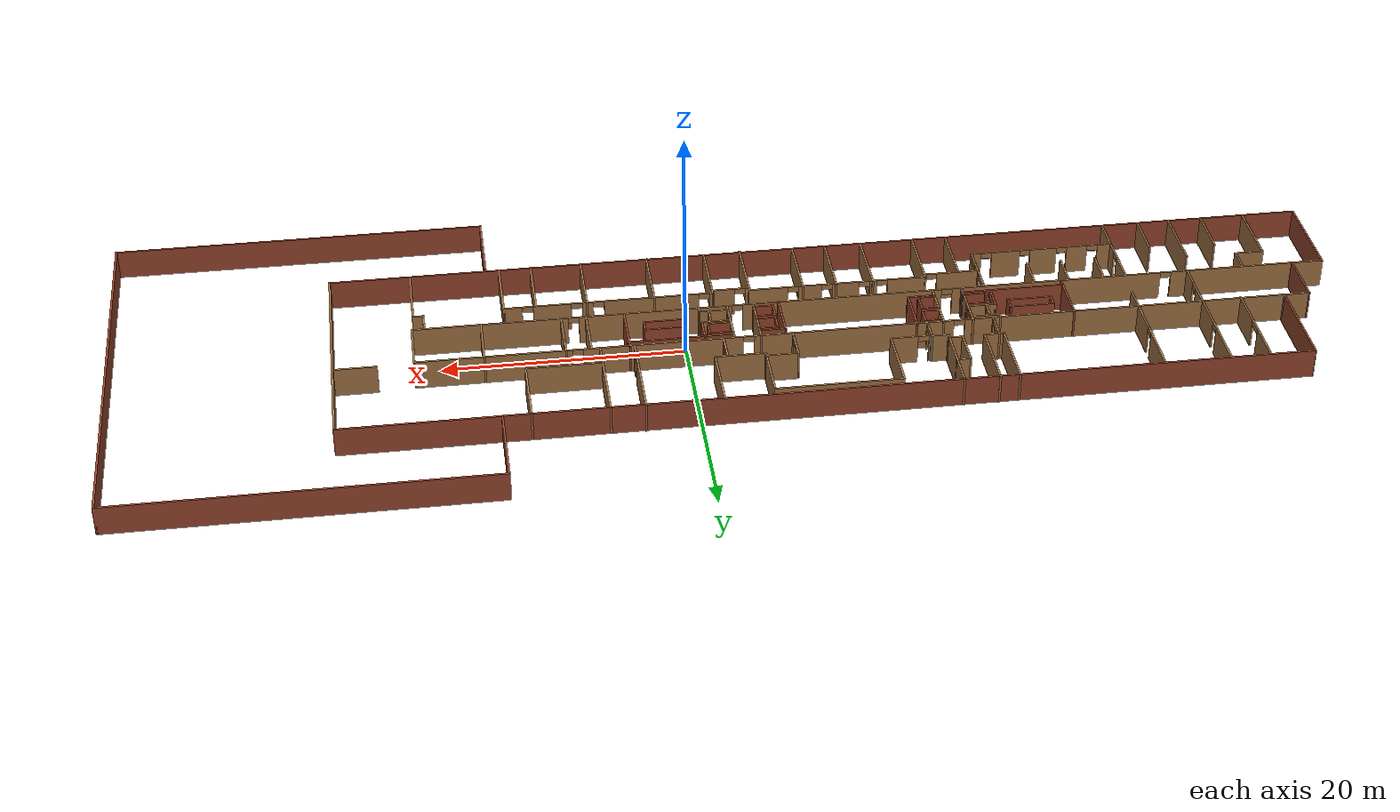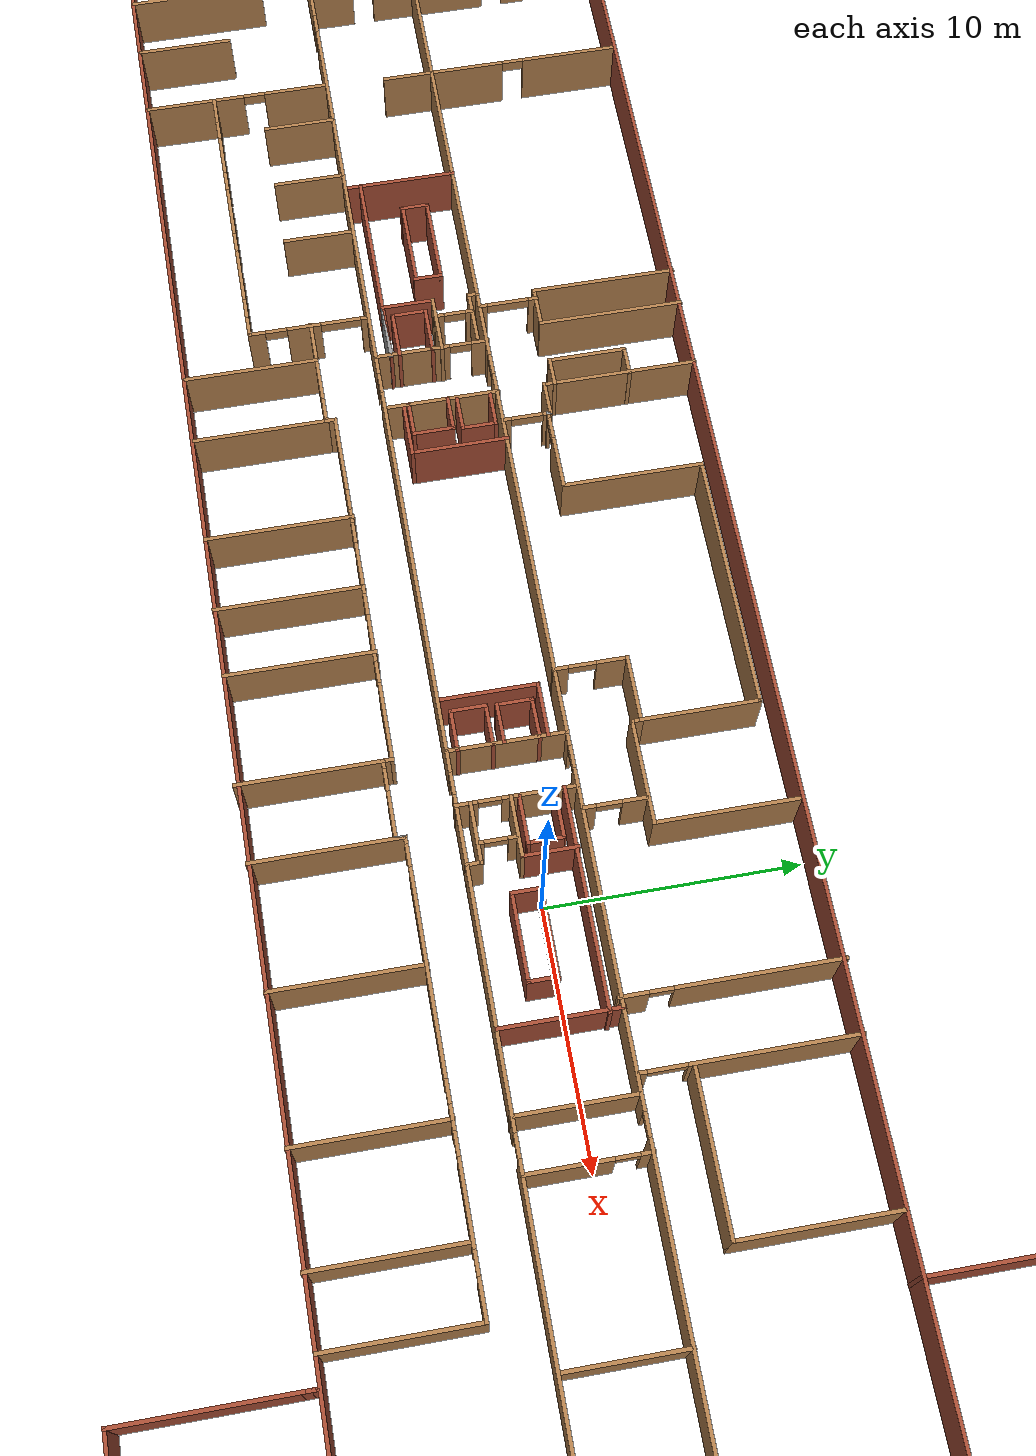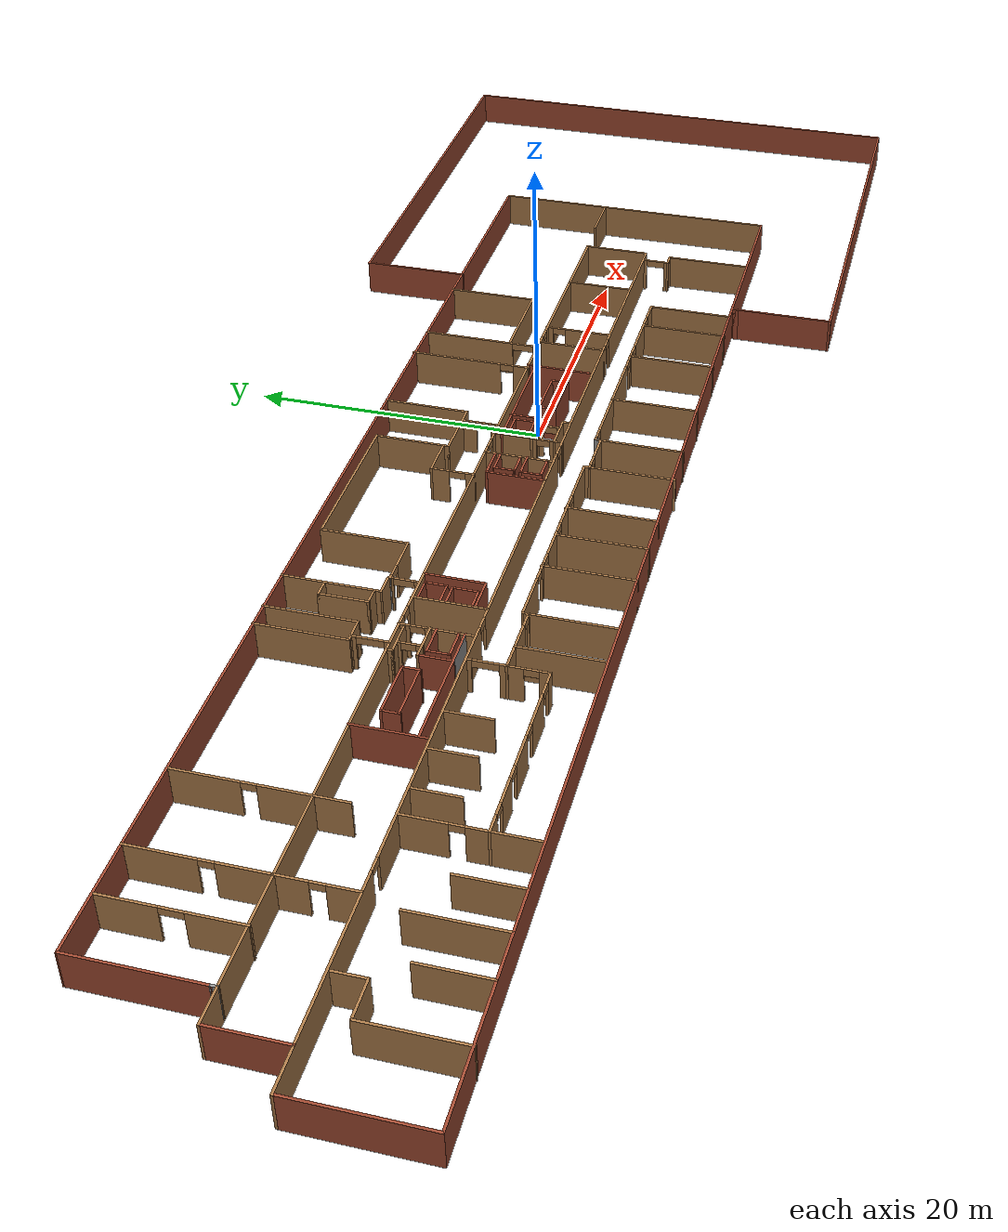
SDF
<?xml version='1.0'?>
<sdf version='1.6'>
  <model name='third_floor'>
    <pose frame=''>-4.00866 -0.044756 0 0 -0 0</pose>
    <link name='Wall_10'>
      <collision name='Wall_10_Collision'>
        <geometry>
          <box>
            <size>2.28863 0.15 2.5</size>
          </box>
        </geometry>
        <pose frame=''>0 0 1.25 0 -0 0</pose>
      </collision>
      <visual name='Wall_10_Visual'>
        <pose frame=''>0 0 1.25 0 -0 0</pose>
        <geometry>
          <box>
            <size>2.28863 0.15 2.5</size>
          </box>
        </geometry>
        <material>
          <script>
            <uri>file://media/materials/scripts/gazebo.material</uri>
            <name>Gazebo/Wood</name>
          </script>
          <ambient>1 1 1 1</ambient>
        </material>
      </visual>
      <pose frame=''>-46.7968 2.06319 0 0 0 -0.001948</pose>
    </link>
    <link name='Wall_100'>
      <collision name='Wall_100_Collision'>
        <geometry>
          <box>
            <size>4.75 0.15 2.5</size>
          </box>
        </geometry>
        <pose frame=''>0 0 1.25 0 -0 0</pose>
      </collision>
      <visual name='Wall_100_Visual'>
        <pose frame=''>0 0 1.25 0 -0 0</pose>
        <geometry>
          <box>
            <size>4.75 0.15 2.5</size>
          </box>
        </geometry>
        <material>
          <script>
            <uri>file://media/materials/scripts/gazebo.material</uri>
            <name>Gazebo/Wood</name>
          </script>
          <ambient>1 1 1 1</ambient>
        </material>
      </visual>
      <pose frame=''>11.9099 -0.263798 0 0 -0 1.5708</pose>
    </link>
    <link name='Wall_102'>
      <collision name='Wall_102_Collision'>
        <geometry>
          <box>
            <size>4.75 0.15 2.5</size>
          </box>
        </geometry>
        <pose frame=''>0 0 1.25 0 -0 0</pose>
      </collision>
      <visual name='Wall_102_Visual'>
        <pose frame=''>0 0 1.25 0 -0 0</pose>
        <geometry>
          <box>
            <size>4.75 0.15 2.5</size>
          </box>
        </geometry>
        <material>
          <script>
            <uri>file://media/materials/scripts/gazebo.material</uri>
            <name>Gazebo/Bricks</name>
          </script>
          <ambient>1 1 1 1</ambient>
        </material>
      </visual>
      <pose frame=''>8.79281 -0.211406 0 0 0 -1.5708</pose>
    </link>
    <link name='Wall_104'>
      <collision name='Wall_104_Collision'>
        <geometry>
          <box>
            <size>4.7023 0.15 2.5</size>
          </box>
        </geometry>
        <pose frame=''>0 0 1.25 0 -0 0</pose>
      </collision>
      <visual name='Wall_104_Visual'>
        <pose frame=''>0 0 1.25 0 -0 0</pose>
        <geometry>
          <box>
            <size>4.7023 0.15 2.5</size>
          </box>
        </geometry>
        <material>
          <script>
            <uri>file://media/materials/scripts/gazebo.material</uri>
            <name>Gazebo/Wood</name>
          </script>
          <ambient>1 1 1 1</ambient>
        </material>
      </visual>
      <pose frame=''>-1.90234 -0.212 0 0 0 -1.57315</pose>
    </link>
    <link name='Wall_106'>
      <pose frame=''>0.278929 -0.25793 0 0 0 -1.5708</pose>
      <visual name='Wall_106_Visual_0'>
        <pose frame=''>-0.899616 0 1.25 0 -0 0</pose>
        <geometry>
          <box>
            <size>2.95077 0.15 2.5</size>
          </box>
        </geometry>
        <material>
          <script>
            <uri>file://media/materials/scripts/gazebo.material</uri>
            <name>Gazebo/Wood</name>
          </script>
          <ambient>1 1 1 1</ambient>
        </material>
      </visual>
      <collision name='Wall_106_Collision_0'>
        <geometry>
          <box>
            <size>2.95077 0.15 2.5</size>
          </box>
        </geometry>
        <pose frame=''>-0.899616 0 1.25 0 -0 0</pose>
      </collision>
      <visual name='Wall_106_Visual_1'>
        <pose frame=''>1.92538 0 1.25 0 -0 0</pose>
        <geometry>
          <box>
            <size>0.899232 0.15 2.5</size>
          </box>
        </geometry>
        <material>
          <script>
            <uri>file://media/materials/scripts/gazebo.material</uri>
            <name>Gazebo/Wood</name>
          </script>
          <ambient>1 1 1 1</ambient>
        </material>
      </visual>
      <collision name='Wall_106_Collision_1'>
        <geometry>
          <box>
            <size>0.899232 0.15 2.5</size>
          </box>
        </geometry>
        <pose frame=''>1.92538 0 1.25 0 -0 0</pose>
      </collision>
      <visual name='Wall_106_Visual_2'>
        <pose frame=''>1.02577 0 2.25 0 -0 0</pose>
        <geometry>
          <box>
            <size>0.9 0.15 0.5</size>
          </box>
        </geometry>
        <material>
          <script>
            <uri>file://media/materials/scripts/gazebo.material</uri>
            <name>Gazebo/Wood</name>
          </script>
          <ambient>1 1 1 1</ambient>
        </material>
      </visual>
      <collision name='Wall_106_Collision_2'>
        <geometry>
          <box>
            <size>0.9 0.15 0.5</size>
          </box>
        </geometry>
        <pose frame=''>1.02577 0 2.25 0 -0 0</pose>
      </collision>
    </link>
    <link name='Wall_112'>
      <collision name='Wall_112_Collision'>
        <geometry>
          <box>
            <size>2.25 0.15 2.5</size>
          </box>
        </geometry>
        <pose frame=''>0 0 1.25 0 -0 0</pose>
      </collision>
      <visual name='Wall_112_Visual'>
        <pose frame=''>0 0 1.25 0 -0 0</pose>
        <geometry>
          <box>
            <size>2.25 0.15 2.5</size>
          </box>
        </geometry>
        <material>
          <script>
            <uri>file://media/materials/scripts/gazebo.material</uri>
            <name>Gazebo/Bricks</name>
          </script>
          <ambient>1 1 1 1</ambient>
        </material>
      </visual>
      <pose frame=''>-2.9577 1.34421 0 0 -0 3.14159</pose>
    </link>
    <link name='Wall_113'>
      <collision name='Wall_113_Collision'>
        <geometry>
          <box>
            <size>4 0.15 2.5</size>
          </box>
        </geometry>
        <pose frame=''>0 0 1.25 0 -0 0</pose>
      </collision>
      <visual name='Wall_113_Visual'>
        <pose frame=''>0 0 1.25 0 -0 0</pose>
        <geometry>
          <box>
            <size>4 0.15 2.5</size>
          </box>
        </geometry>
        <material>
          <script>
            <uri>file://media/materials/scripts/gazebo.material</uri>
            <name>Gazebo/Bricks</name>
          </script>
          <ambient>1 1 1 1</ambient>
        </material>
      </visual>
      <pose frame=''>-4.00769 -0.580789 0 0 0 -1.5708</pose>
    </link>
    <link name='Wall_115'>
      <collision name='Wall_115_Collision'>
        <geometry>
          <box>
            <size>1.75 0.15 2.5</size>
          </box>
        </geometry>
        <pose frame=''>0 0 1.25 0 -0 0</pose>
      </collision>
      <visual name='Wall_115_Visual'>
        <pose frame=''>0 0 1.25 0 -0 0</pose>
        <geometry>
          <box>
            <size>1.75 0.15 2.5</size>
          </box>
        </geometry>
        <material>
          <script>
            <uri>file://media/materials/scripts/gazebo.material</uri>
            <name>Gazebo/Bricks</name>
          </script>
          <ambient>1 1 1 1</ambient>
        </material>
      </visual>
      <pose frame=''>-2.68443 -0.772627 0 0 -0 3.14159</pose>
    </link>
    <link name='Wall_116'>
      <collision name='Wall_116_Collision'>
        <geometry>
          <box>
            <size>1.5 0.15 2.5</size>
          </box>
        </geometry>
        <pose frame=''>0 0 1.25 0 -0 0</pose>
      </collision>
      <visual name='Wall_116_Visual'>
        <pose frame=''>0 0 1.25 0 -0 0</pose>
        <geometry>
          <box>
            <size>1.5 0.15 2.5</size>
          </box>
        </geometry>
        <material>
          <script>
            <uri>file://media/materials/scripts/gazebo.material</uri>
            <name>Gazebo/Bricks</name>
          </script>
          <ambient>1 1 1 1</ambient>
        </material>
      </visual>
      <pose frame=''>-3.48443 -1.44763 0 0 0 -1.5708</pose>
    </link>
    <link name='Wall_117'>
      <collision name='Wall_117_Collision'>
        <geometry>
          <box>
            <size>1.75 0.15 2.5</size>
          </box>
        </geometry>
        <pose frame=''>0 0 1.25 0 -0 0</pose>
      </collision>
      <visual name='Wall_117_Visual'>
        <pose frame=''>0 0 1.25 0 -0 0</pose>
        <geometry>
          <box>
            <size>1.75 0.15 2.5</size>
          </box>
        </geometry>
        <material>
          <script>
            <uri>file://media/materials/scripts/gazebo.material</uri>
            <name>Gazebo/Bricks</name>
          </script>
          <ambient>1 1 1 1</ambient>
        </material>
      </visual>
      <pose frame=''>-2.68443 -2.12263 0 0 -0 0</pose>
    </link>
    <link name='Wall_119'>
      <collision name='Wall_119_Collision'>
        <geometry>
          <box>
            <size>1.67343 0.15 2.5</size>
          </box>
        </geometry>
        <pose frame=''>0 0 1.25 0 -0 0</pose>
      </collision>
      <visual name='Wall_119_Visual'>
        <pose frame=''>0 0 1.25 0 -0 0</pose>
        <geometry>
          <box>
            <size>1.67343 0.15 2.5</size>
          </box>
        </geometry>
        <material>
          <script>
            <uri>file://media/materials/scripts/gazebo.material</uri>
            <name>Gazebo/Bricks</name>
          </script>
          <ambient>1 1 1 1</ambient>
        </material>
      </visual>
      <pose frame=''>-2.67619 -0.351698 0 0 0 -3.13869</pose>
    </link>
    <link name='Wall_120'>
      <collision name='Wall_120_Collision'>
        <geometry>
          <box>
            <size>1.5 0.15 2.5</size>
          </box>
        </geometry>
        <pose frame=''>0 0 1.25 0 -0 0</pose>
      </collision>
      <visual name='Wall_120_Visual'>
        <pose frame=''>0 0 1.25 0 -0 0</pose>
        <geometry>
          <box>
            <size>1.5 0.15 2.5</size>
          </box>
        </geometry>
        <material>
          <script>
            <uri>file://media/materials/scripts/gazebo.material</uri>
            <name>Gazebo/Bricks</name>
          </script>
          <ambient>1 1 1 1</ambient>
        </material>
      </visual>
      <pose frame=''>-3.43791 0.321088 0 0 -0 1.5708</pose>
    </link>
    <link name='Wall_125'>
      <collision name='Wall_125_Collision'>
        <geometry>
          <box>
            <size>2.47053 0.15 2.5</size>
          </box>
        </geometry>
        <pose frame=''>0 0 1.25 0 -0 0</pose>
      </collision>
      <visual name='Wall_125_Visual'>
        <pose frame=''>0 0 1.25 0 -0 0</pose>
        <geometry>
          <box>
            <size>2.47053 0.15 2.5</size>
          </box>
        </geometry>
        <material>
          <script>
            <uri>file://media/materials/scripts/gazebo.material</uri>
            <name>Gazebo/Wood</name>
          </script>
          <ambient>1 1 1 1</ambient>
        </material>
      </visual>
      <pose frame=''>1.43919 -2.00551 0 0 -0 0</pose>
    </link>
    <link name='Wall_126'>
      <collision name='Wall_126_Collision'>
        <geometry>
          <box>
            <size>0.685462 0.15 2.5</size>
          </box>
        </geometry>
        <pose frame=''>0 0 1.25 0 -0 0</pose>
      </collision>
      <visual name='Wall_126_Visual'>
        <pose frame=''>0 0 1.25 0 -0 0</pose>
        <geometry>
          <box>
            <size>0.685462 0.15 2.5</size>
          </box>
        </geometry>
        <material>
          <script>
            <uri>file://media/materials/scripts/gazebo.material</uri>
            <name>Gazebo/Wood</name>
          </script>
          <ambient>1 1 1 1</ambient>
        </material>
      </visual>
      <pose frame=''>2.61019 -2.27285 0 0 0 -1.5591</pose>
    </link>
    <link name='Wall_129'>
      <collision name='Wall_129_Collision'>
        <geometry>
          <box>
            <size>1.69095 0.15 2.5</size>
          </box>
        </geometry>
        <pose frame=''>0 0 1.25 0 -0 0</pose>
      </collision>
      <visual name='Wall_129_Visual'>
        <pose frame=''>0 0 1.25 0 -0 0</pose>
        <geometry>
          <box>
            <size>1.69095 0.15 2.5</size>
          </box>
        </geometry>
        <material>
          <script>
            <uri>file://media/materials/scripts/gazebo.material</uri>
            <name>Gazebo/Bricks</name>
          </script>
          <ambient>1 1 1 1</ambient>
        </material>
      </visual>
      <pose frame=''>-2.66745 1.00541 0 0 -0 0.012104</pose>
    </link>
    <link name='Wall_13'>
      <collision name='Wall_13_Collision'>
        <geometry>
          <box>
            <size>0.46611 0.15 2.5</size>
          </box>
        </geometry>
        <pose frame=''>0 0 1.25 0 -0 0</pose>
      </collision>
      <visual name='Wall_13_Visual'>
        <pose frame=''>0 0 1.25 0 -0 0</pose>
        <geometry>
          <box>
            <size>0.46611 0.15 2.5</size>
          </box>
        </geometry>
        <material>
          <script>
            <uri>file://media/materials/scripts/gazebo.material</uri>
            <name>Gazebo/Grey</name>
          </script>
          <ambient>1 1 1 1</ambient>
        </material>
      </visual>
      <pose frame=''>-45.7292 2.21916 0 0 -0 1.58134</pose>
    </link>
    <link name='Wall_132'>
      <collision name='Wall_132_Collision'>
        <geometry>
          <box>
            <size>4.75 0.15 2.5</size>
          </box>
        </geometry>
        <pose frame=''>0 0 1.25 0 -0 0</pose>
      </collision>
      <visual name='Wall_132_Visual'>
        <pose frame=''>0 0 1.25 0 -0 0</pose>
        <geometry>
          <box>
            <size>4.75 0.15 2.5</size>
          </box>
        </geometry>
        <material>
          <script>
            <uri>file://media/materials/scripts/gazebo.material</uri>
            <name>Gazebo/Wood</name>
          </script>
          <ambient>1 1 1 1</ambient>
        </material>
      </visual>
      <pose frame=''>-16.9641 -0.197269 0 0 0 -1.5708</pose>
    </link>
    <link name='Wall_134'>
      <pose frame=''>-19.4066 -0.197269 0 0 0 -1.5708</pose>
      <visual name='Wall_134_Visual_0'>
        <pose frame=''>-1.99521 0 1.25 0 -0 0</pose>
        <geometry>
          <box>
            <size>0.75958 0.15 2.5</size>
          </box>
        </geometry>
        <material>
          <script>
            <uri>file://media/materials/scripts/gazebo.material</uri>
            <name>Gazebo/Wood</name>
          </script>
          <ambient>1 1 1 1</ambient>
        </material>
      </visual>
      <collision name='Wall_134_Collision_0'>
        <geometry>
          <box>
            <size>0.75958 0.15 2.5</size>
          </box>
        </geometry>
        <pose frame=''>-1.99521 0 1.25 0 -0 0</pose>
      </collision>
      <visual name='Wall_134_Visual_1'>
        <pose frame=''>0.82979 0 1.25 0 -0 0</pose>
        <geometry>
          <box>
            <size>3.09042 0.15 2.5</size>
          </box>
        </geometry>
        <material>
          <script>
            <uri>file://media/materials/scripts/gazebo.material</uri>
            <name>Gazebo/Wood</name>
          </script>
          <ambient>1 1 1 1</ambient>
        </material>
      </visual>
      <collision name='Wall_134_Collision_1'>
        <geometry>
          <box>
            <size>3.09042 0.15 2.5</size>
          </box>
        </geometry>
        <pose frame=''>0.82979 0 1.25 0 -0 0</pose>
      </collision>
      <visual name='Wall_134_Visual_2'>
        <pose frame=''>-1.16542 0 2.25 0 -0 0</pose>
        <geometry>
          <box>
            <size>0.9 0.15 0.5</size>
          </box>
        </geometry>
        <material>
          <script>
            <uri>file://media/materials/scripts/gazebo.material</uri>
            <name>Gazebo/Wood</name>
          </script>
          <ambient>1 1 1 1</ambient>
        </material>
      </visual>
      <collision name='Wall_134_Collision_2'>
        <geometry>
          <box>
            <size>0.9 0.15 0.5</size>
          </box>
        </geometry>
        <pose frame=''>-1.16542 0 2.25 0 -0 0</pose>
      </collision>
    </link>
    <link name='Wall_136'>
      <collision name='Wall_136_Collision'>
        <geometry>
          <box>
            <size>2.5 0.15 2.5</size>
          </box>
        </geometry>
        <pose frame=''>0 0 1.25 0 -0 0</pose>
      </collision>
      <visual name='Wall_136_Visual'>
        <pose frame=''>0 0 1.25 0 -0 0</pose>
        <geometry>
          <box>
            <size>2.5 0.15 2.5</size>
          </box>
        </geometry>
        <material>
          <script>
            <uri>file://media/materials/scripts/gazebo.material</uri>
            <name>Gazebo/Wood</name>
          </script>
          <ambient>1 1 1 1</ambient>
        </material>
      </visual>
      <pose frame=''>-20.5351 0.19525 0 0 -0 3.14159</pose>
    </link>
    <link name='Wall_137'>
      <collision name='Wall_137_Collision'>
        <geometry>
          <box>
            <size>2.25 0.15 2.5</size>
          </box>
        </geometry>
        <pose frame=''>0 0 1.25 0 -0 0</pose>
      </collision>
      <visual name='Wall_137_Visual'>
        <pose frame=''>0 0 1.25 0 -0 0</pose>
        <geometry>
          <box>
            <size>2.25 0.15 2.5</size>
          </box>
        </geometry>
        <material>
          <script>
            <uri>file://media/materials/scripts/gazebo.material</uri>
            <name>Gazebo/Bricks</name>
          </script>
          <ambient>1 1 1 1</ambient>
        </material>
      </visual>
      <pose frame=''>-21.7101 -0.85475 0 0 0 -1.5708</pose>
    </link>
    <link name='Wall_138'>
      <collision name='Wall_138_Collision'>
        <geometry>
          <box>
            <size>2.5 0.15 2.5</size>
          </box>
        </geometry>
        <pose frame=''>0 0 1.25 0 -0 0</pose>
      </collision>
      <visual name='Wall_138_Visual'>
        <pose frame=''>0 0 1.25 0 -0 0</pose>
        <geometry>
          <box>
            <size>2.5 0.15 2.5</size>
          </box>
        </geometry>
        <material>
          <script>
            <uri>file://media/materials/scripts/gazebo.material</uri>
            <name>Gazebo/Grey</name>
          </script>
          <ambient>1 1 1 1</ambient>
        </material>
      </visual>
      <pose frame=''>-20.5351 -1.90475 0 0 -0 0</pose>
    </link>
    <link name='Wall_140'>
      <collision name='Wall_140_Collision'>
        <geometry>
          <box>
            <size>2 0.15 2.5</size>
          </box>
        </geometry>
        <pose frame=''>0 0 1.25 0 -0 0</pose>
      </collision>
      <visual name='Wall_140_Visual'>
        <pose frame=''>0 0 1.25 0 -0 0</pose>
        <geometry>
          <box>
            <size>2 0.15 2.5</size>
          </box>
        </geometry>
        <material>
          <script>
            <uri>file://media/materials/scripts/gazebo.material</uri>
            <name>Gazebo/Bricks</name>
          </script>
          <ambient>1 1 1 1</ambient>
        </material>
      </visual>
      <pose frame=''>1.24453 -0.176941 0 0 -0 0</pose>
    </link>
    <link name='Wall_141'>
      <collision name='Wall_141_Collision'>
        <geometry>
          <box>
            <size>1.5 0.15 2.5</size>
          </box>
        </geometry>
        <pose frame=''>0 0 1.25 0 -0 0</pose>
      </collision>
      <visual name='Wall_141_Visual'>
        <pose frame=''>0 0 1.25 0 -0 0</pose>
        <geometry>
          <box>
            <size>1.5 0.15 2.5</size>
          </box>
        </geometry>
        <material>
          <script>
            <uri>file://media/materials/scripts/gazebo.material</uri>
            <name>Gazebo/Bricks</name>
          </script>
          <ambient>1 1 1 1</ambient>
        </material>
      </visual>
      <pose frame=''>2.16953 0.498059 0 0 -0 1.5708</pose>
    </link>
    <link name='Wall_142'>
      <collision name='Wall_142_Collision'>
        <geometry>
          <box>
            <size>2 0.15 2.5</size>
          </box>
        </geometry>
        <pose frame=''>0 0 1.25 0 -0 0</pose>
      </collision>
      <visual name='Wall_142_Visual'>
        <pose frame=''>0 0 1.25 0 -0 0</pose>
        <geometry>
          <box>
            <size>2 0.15 2.5</size>
          </box>
        </geometry>
        <material>
          <script>
            <uri>file://media/materials/scripts/gazebo.material</uri>
            <name>Gazebo/Bricks</name>
          </script>
          <ambient>1 1 1 1</ambient>
        </material>
      </visual>
      <pose frame=''>1.24453 1.17306 0 0 -0 3.14159</pose>
    </link>
    <link name='Wall_144'>
      <pose frame=''>1.85514 -1.2369 0 0 0 -1.5708</pose>
      <visual name='Wall_144_Visual_0'>
        <pose frame=''>-0.55326 0 1.25 0 -0 0</pose>
        <geometry>
          <box>
            <size>0.393481 0.15 2.5</size>
          </box>
        </geometry>
        <material>
          <script>
            <uri>file://media/materials/scripts/gazebo.material</uri>
            <name>Gazebo/Wood</name>
          </script>
          <ambient>1 1 1 1</ambient>
        </material>
      </visual>
      <collision name='Wall_144_Collision_0'>
        <geometry>
          <box>
            <size>0.393481 0.15 2.5</size>
          </box>
        </geometry>
        <pose frame=''>-0.55326 0 1.25 0 -0 0</pose>
      </collision>
      <visual name='Wall_144_Visual_1'>
        <pose frame=''>0.64674 0 1.25 0 -0 0</pose>
        <geometry>
          <box>
            <size>0.206519 0.15 2.5</size>
          </box>
        </geometry>
        <material>
          <script>
            <uri>file://media/materials/scripts/gazebo.material</uri>
            <name>Gazebo/Wood</name>
          </script>
          <ambient>1 1 1 1</ambient>
        </material>
      </visual>
      <collision name='Wall_144_Collision_1'>
        <geometry>
          <box>
            <size>0.206519 0.15 2.5</size>
          </box>
        </geometry>
        <pose frame=''>0.64674 0 1.25 0 -0 0</pose>
      </collision>
      <visual name='Wall_144_Visual_2'>
        <pose frame=''>0.093481 0 2.25 0 -0 0</pose>
        <geometry>
          <box>
            <size>0.9 0.15 0.5</size>
          </box>
        </geometry>
        <material>
          <script>
            <uri>file://media/materials/scripts/gazebo.material</uri>
            <name>Gazebo/Wood</name>
          </script>
          <ambient>1 1 1 1</ambient>
        </material>
      </visual>
      <collision name='Wall_144_Collision_2'>
        <geometry>
          <box>
            <size>0.9 0.15 0.5</size>
          </box>
        </geometry>
        <pose frame=''>0.093481 0 2.25 0 -0 0</pose>
      </collision>
    </link>
    <link name='Wall_146'>
      <collision name='Wall_146_Collision'>
        <geometry>
          <box>
            <size>2 0.15 2.5</size>
          </box>
        </geometry>
        <pose frame=''>0 0 1.25 0 -0 0</pose>
      </collision>
      <visual name='Wall_146_Visual'>
        <pose frame=''>0 0 1.25 0 -0 0</pose>
        <geometry>
          <box>
            <size>2 0.15 2.5</size>
          </box>
        </geometry>
        <material>
          <script>
            <uri>file://media/materials/scripts/gazebo.material</uri>
            <name>Gazebo/Bricks</name>
          </script>
          <ambient>1 1 1 1</ambient>
        </material>
      </visual>
      <pose frame=''>-20.3056 -0.187196 0 0 -0 3.14159</pose>
    </link>
    <link name='Wall_147'>
      <collision name='Wall_147_Collision'>
        <geometry>
          <box>
            <size>1.51744 0.15 2.5</size>
          </box>
        </geometry>
        <pose frame=''>0 0 1.25 0 -0 0</pose>
      </collision>
      <visual name='Wall_147_Visual'>
        <pose frame=''>0 0 1.25 0 -0 0</pose>
        <geometry>
          <box>
            <size>1.51744 0.15 2.5</size>
          </box>
        </geometry>
        <material>
          <script>
            <uri>file://media/materials/scripts/gazebo.material</uri>
            <name>Gazebo/Bricks</name>
          </script>
          <ambient>1 1 1 1</ambient>
        </material>
      </visual>
      <pose frame=''>-21.2496 -0.870915 0 0 0 -1.56855</pose>
    </link>
    <link name='Wall_148'>
      <collision name='Wall_148_Collision'>
        <geometry>
          <box>
            <size>2 0.15 2.5</size>
          </box>
        </geometry>
        <pose frame=''>0 0 1.25 0 -0 0</pose>
      </collision>
      <visual name='Wall_148_Visual'>
        <pose frame=''>0 0 1.25 0 -0 0</pose>
        <geometry>
          <box>
            <size>2 0.15 2.5</size>
          </box>
        </geometry>
        <material>
          <script>
            <uri>file://media/materials/scripts/gazebo.material</uri>
            <name>Gazebo/Bricks</name>
          </script>
          <ambient>1 1 1 1</ambient>
        </material>
      </visual>
      <pose frame=''>-20.3128 -1.55463 0 0 -0 0</pose>
    </link>
    <link name='Wall_15'>
      <collision name='Wall_15_Collision'>
        <geometry>
          <box>
            <size>7.5 0.15 2.5</size>
          </box>
        </geometry>
        <pose frame=''>0 0 1.25 0 -0 0</pose>
      </collision>
      <visual name='Wall_15_Visual'>
        <pose frame=''>0 0 1.25 0 -0 0</pose>
        <geometry>
          <box>
            <size>7.5 0.15 2.5</size>
          </box>
        </geometry>
        <material>
          <script>
            <uri>file://media/materials/scripts/gazebo.material</uri>
            <name>Gazebo/Bricks</name>
          </script>
          <ambient>1 1 1 1</ambient>
        </material>
      </visual>
      <pose frame=''>19.6276 13.875 0 0 -0 1.5708</pose>
    </link>
    <link name='Wall_150'>
      <collision name='Wall_150_Collision'>
        <geometry>
          <box>
            <size>1.5 0.15 2.5</size>
          </box>
        </geometry>
        <pose frame=''>0 0 1.25 0 -0 0</pose>
      </collision>
      <visual name='Wall_150_Visual'>
        <pose frame=''>0 0 1.25 0 -0 0</pose>
        <geometry>
          <box>
            <size>1.5 0.15 2.5</size>
          </box>
        </geometry>
        <material>
          <script>
            <uri>file://media/materials/scripts/gazebo.material</uri>
            <name>Gazebo/Bricks</name>
          </script>
          <ambient>1 1 1 1</ambient>
        </material>
      </visual>
      <pose frame=''>-16.1961 0.404608 0 0 -0 0</pose>
    </link>
    <link name='Wall_151'>
      <collision name='Wall_151_Collision'>
        <geometry>
          <box>
            <size>1.5 0.15 2.5</size>
          </box>
        </geometry>
        <pose frame=''>0 0 1.25 0 -0 0</pose>
      </collision>
      <visual name='Wall_151_Visual'>
        <pose frame=''>0 0 1.25 0 -0 0</pose>
        <geometry>
          <box>
            <size>1.5 0.15 2.5</size>
          </box>
        </geometry>
        <material>
          <script>
            <uri>file://media/materials/scripts/gazebo.material</uri>
            <name>Gazebo/Bricks</name>
          </script>
          <ambient>1 1 1 1</ambient>
        </material>
      </visual>
      <pose frame=''>-15.5211 1.07961 0 0 -0 1.5708</pose>
    </link>
    <link name='Wall_152'>
      <collision name='Wall_152_Collision'>
        <geometry>
          <box>
            <size>1.5 0.15 2.5</size>
          </box>
        </geometry>
        <pose frame=''>0 0 1.25 0 -0 0</pose>
      </collision>
      <visual name='Wall_152_Visual'>
        <pose frame=''>0 0 1.25 0 -0 0</pose>
        <geometry>
          <box>
            <size>1.5 0.15 2.5</size>
          </box>
        </geometry>
        <material>
          <script>
            <uri>file://media/materials/scripts/gazebo.material</uri>
            <name>Gazebo/Bricks</name>
          </script>
          <ambient>1 1 1 1</ambient>
        </material>
      </visual>
      <pose frame=''>-16.1961 1.75461 0 0 -0 3.14159</pose>
    </link>
    <link name='Wall_154'>
      <collision name='Wall_154_Collision'>
        <geometry>
          <box>
            <size>1.5 0.15 2.5</size>
          </box>
        </geometry>
        <pose frame=''>0 0 1.25 0 -0 0</pose>
      </collision>
      <visual name='Wall_154_Visual'>
        <pose frame=''>0 0 1.25 0 -0 0</pose>
        <geometry>
          <box>
            <size>1.5 0.15 2.5</size>
          </box>
        </geometry>
        <material>
          <script>
            <uri>file://media/materials/scripts/gazebo.material</uri>
            <name>Gazebo/Bricks</name>
          </script>
          <ambient>1 1 1 1</ambient>
        </material>
      </visual>
      <pose frame=''>-16.2658 0.032417 0 0 -0 0</pose>
    </link>
    <link name='Wall_155'>
      <collision name='Wall_155_Collision'>
        <geometry>
          <box>
            <size>1.75 0.15 2.5</size>
          </box>
        </geometry>
        <pose frame=''>0 0 1.25 0 -0 0</pose>
      </collision>
      <visual name='Wall_155_Visual'>
        <pose frame=''>0 0 1.25 0 -0 0</pose>
        <geometry>
          <box>
            <size>1.75 0.15 2.5</size>
          </box>
        </geometry>
        <material>
          <script>
            <uri>file://media/materials/scripts/gazebo.material</uri>
            <name>Gazebo/Bricks</name>
          </script>
          <ambient>1 1 1 1</ambient>
        </material>
      </visual>
      <pose frame=''>-15.5908 -0.767583 0 0 0 -1.5708</pose>
    </link>
    <link name='Wall_156'>
      <collision name='Wall_156_Collision'>
        <geometry>
          <box>
            <size>1.5 0.15 2.5</size>
          </box>
        </geometry>
        <pose frame=''>0 0 1.25 0 -0 0</pose>
      </collision>
      <visual name='Wall_156_Visual'>
        <pose frame=''>0 0 1.25 0 -0 0</pose>
        <geometry>
          <box>
            <size>1.5 0.15 2.5</size>
          </box>
        </geometry>
        <material>
          <script>
            <uri>file://media/materials/scripts/gazebo.material</uri>
            <name>Gazebo/Bricks</name>
          </script>
          <ambient>1 1 1 1</ambient>
        </material>
      </visual>
      <pose frame=''>-16.2658 -1.56758 0 0 -0 3.14159</pose>
    </link>
    <link name='Wall_158'>
      <collision name='Wall_158_Collision'>
        <geometry>
          <box>
            <size>4 0.15 2.5</size>
          </box>
        </geometry>
        <pose frame=''>0 0 1.25 0 -0 0</pose>
      </collision>
      <visual name='Wall_158_Visual'>
        <pose frame=''>0 0 1.25 0 -0 0</pose>
        <geometry>
          <box>
            <size>4 0.15 2.5</size>
          </box>
        </geometry>
        <material>
          <script>
            <uri>file://media/materials/scripts/gazebo.material</uri>
            <name>Gazebo/Bricks</name>
          </script>
          <ambient>1 1 1 1</ambient>
        </material>
      </visual>
      <pose frame=''>-14.7542 0.154469 0 0 0 -1.5708</pose>
    </link>
    <link name='Wall_159'>
      <collision name='Wall_159_Collision'>
        <geometry>
          <box>
            <size>2.25 0.15 2.5</size>
          </box>
        </geometry>
        <pose frame=''>0 0 1.25 0 -0 0</pose>
      </collision>
      <visual name='Wall_159_Visual'>
        <pose frame=''>0 0 1.25 0 -0 0</pose>
        <geometry>
          <box>
            <size>2.25 0.15 2.5</size>
          </box>
        </geometry>
        <material>
          <script>
            <uri>file://media/materials/scripts/gazebo.material</uri>
            <name>Gazebo/Bricks</name>
          </script>
          <ambient>1 1 1 1</ambient>
        </material>
      </visual>
      <pose frame=''>-15.8042 -1.77053 0 0 -0 3.14159</pose>
    </link>
    <link name='Wall_16'>
      <collision name='Wall_16_Collision'>
        <geometry>
          <box>
            <size>31 0.15 2.5</size>
          </box>
        </geometry>
        <pose frame=''>0 0 1.25 0 -0 0</pose>
      </collision>
      <visual name='Wall_16_Visual'>
        <pose frame=''>0 0 1.25 0 -0 0</pose>
        <geometry>
          <box>
            <size>31 0.15 2.5</size>
          </box>
        </geometry>
        <material>
          <script>
            <uri>file://media/materials/scripts/gazebo.material</uri>
            <name>Gazebo/Bricks</name>
          </script>
          <ambient>1 1 1 1</ambient>
        </material>
      </visual>
      <pose frame=''>35.0526 17.55 0 0 -0 0</pose>
    </link>
    <link name='Wall_162'>
      <collision name='Wall_162_Collision'>
        <geometry>
          <box>
            <size>0.5 0.15 2.5</size>
          </box>
        </geometry>
        <pose frame=''>0 0 1.25 0 -0 0</pose>
      </collision>
      <visual name='Wall_162_Visual'>
        <pose frame=''>0 0 1.25 0 -0 0</pose>
        <geometry>
          <box>
            <size>0.5 0.15 2.5</size>
          </box>
        </geometry>
        <material>
          <script>
            <uri>file://media/materials/scripts/gazebo.material</uri>
            <name>Gazebo/Wood</name>
          </script>
          <ambient>1 1 1 1</ambient>
        </material>
      </visual>
      <pose frame=''>-21.7009 1.88776 0 0 0 -1.5708</pose>
    </link>
    <link name='Wall_163'>
      <collision name='Wall_163_Collision'>
        <geometry>
          <box>
            <size>2.25 0.15 2.5</size>
          </box>
        </geometry>
        <pose frame=''>0 0 1.25 0 -0 0</pose>
      </collision>
      <visual name='Wall_163_Visual'>
        <pose frame=''>0 0 1.25 0 -0 0</pose>
        <geometry>
          <box>
            <size>2.25 0.15 2.5</size>
          </box>
        </geometry>
        <material>
          <script>
            <uri>file://media/materials/scripts/gazebo.material</uri>
            <name>Gazebo/Wood</name>
          </script>
          <ambient>1 1 1 1</ambient>
        </material>
      </visual>
      <pose frame=''>-20.6509 1.71276 0 0 -0 0</pose>
    </link>
    <link name='Wall_165'>
      <pose frame=''>-20.9277 0.928618 0 0 0 -1.56979</pose>
      <visual name='Wall_165_Visual_0'>
        <pose frame=''>-0.664878 0 1.25 0 -0 0</pose>
        <geometry>
          <box>
            <size>0.314831 0.15 2.5</size>
          </box>
        </geometry>
        <material>
          <script>
            <uri>file://media/materials/scripts/gazebo.material</uri>
            <name>Gazebo/Wood</name>
          </script>
          <ambient>1 1 1 1</ambient>
        </material>
      </visual>
      <collision name='Wall_165_Collision_0'>
        <geometry>
          <box>
            <size>0.314831 0.15 2.5</size>
          </box>
        </geometry>
        <pose frame=''>-0.664878 0 1.25 0 -0 0</pose>
      </collision>
      <visual name='Wall_165_Visual_1'>
        <pose frame=''>0.607416 0 1.25 0 -0 0</pose>
        <geometry>
          <box>
            <size>0.429757 0.15 2.5</size>
          </box>
        </geometry>
        <material>
          <script>
            <uri>file://media/materials/scripts/gazebo.material</uri>
            <name>Gazebo/Wood</name>
          </script>
          <ambient>1 1 1 1</ambient>
        </material>
      </visual>
      <collision name='Wall_165_Collision_1'>
        <geometry>
          <box>
            <size>0.429757 0.15 2.5</size>
          </box>
        </geometry>
        <pose frame=''>0.607416 0 1.25 0 -0 0</pose>
      </collision>
      <visual name='Wall_165_Visual_2'>
        <pose frame=''>-0.057463 0 2.25 0 -0 0</pose>
        <geometry>
          <box>
            <size>0.9 0.15 0.5</size>
          </box>
        </geometry>
        <material>
          <script>
            <uri>file://media/materials/scripts/gazebo.material</uri>
            <name>Gazebo/Wood</name>
          </script>
          <ambient>1 1 1 1</ambient>
        </material>
      </visual>
      <collision name='Wall_165_Collision_2'>
        <geometry>
          <box>
            <size>0.9 0.15 0.5</size>
          </box>
        </geometry>
        <pose frame=''>-0.057463 0 2.25 0 -0 0</pose>
      </collision>
    </link>
    <link name='Wall_168'>
      <collision name='Wall_168_Collision'>
        <geometry>
          <box>
            <size>4.75 0.15 2.5</size>
          </box>
        </geometry>
        <pose frame=''>0 0 1.25 0 -0 0</pose>
      </collision>
      <visual name='Wall_168_Visual'>
        <pose frame=''>0 0 1.25 0 -0 0</pose>
        <geometry>
          <box>
            <size>4.75 0.15 2.5</size>
          </box>
        </geometry>
        <material>
          <script>
            <uri>file://media/materials/scripts/gazebo.material</uri>
            <name>Gazebo/Bricks</name>
          </script>
          <ambient>1 1 1 1</ambient>
        </material>
      </visual>
      <pose frame=''>-27.8909 -0.217787 0 0 0 -1.5708</pose>
    </link>
    <link name='Wall_17'>
      <collision name='Wall_17_Collision'>
        <geometry>
          <box>
            <size>35.25 0.15 2.5</size>
          </box>
        </geometry>
        <pose frame=''>0 0 1.25 0 -0 0</pose>
      </collision>
      <visual name='Wall_17_Visual'>
        <pose frame=''>0 0 1.25 0 -0 0</pose>
        <geometry>
          <box>
            <size>35.25 0.15 2.5</size>
          </box>
        </geometry>
        <material>
          <script>
            <uri>file://media/materials/scripts/gazebo.material</uri>
            <name>Gazebo/Bricks</name>
          </script>
          <ambient>1 1 1 1</ambient>
        </material>
      </visual>
      <pose frame=''>50.4776 -1e-06 0 0 0 -1.5708</pose>
    </link>
    <link name='Wall_172'>
      <collision name='Wall_172_Collision'>
        <geometry>
          <box>
            <size>8.64986 0.15 2.5</size>
          </box>
        </geometry>
        <pose frame=''>0 0 1.25 0 -0 0</pose>
      </collision>
      <visual name='Wall_172_Visual'>
        <pose frame=''>0 0 1.25 0 -0 0</pose>
        <geometry>
          <box>
            <size>8.64986 0.15 2.5</size>
          </box>
        </geometry>
        <material>
          <script>
            <uri>file://media/materials/scripts/gazebo.material</uri>
            <name>Gazebo/Bricks</name>
          </script>
          <ambient>1 1 1 1</ambient>
        </material>
      </visual>
      <pose frame=''>-23.61 -1.90275 0 0 -0 3.14112</pose>
    </link>
    <link name='Wall_18'>
      <collision name='Wall_18_Collision'>
        <geometry>
          <box>
            <size>31 0.15 2.5</size>
          </box>
        </geometry>
        <pose frame=''>0 0 1.25 0 -0 0</pose>
      </collision>
      <visual name='Wall_18_Visual'>
        <pose frame=''>0 0 1.25 0 -0 0</pose>
        <geometry>
          <box>
            <size>31 0.15 2.5</size>
          </box>
        </geometry>
        <material>
          <script>
            <uri>file://media/materials/scripts/gazebo.material</uri>
            <name>Gazebo/Bricks</name>
          </script>
          <ambient>1 1 1 1</ambient>
        </material>
      </visual>
      <pose frame=''>35.0526 -17.55 0 0 -0 3.14159</pose>
    </link>
    <link name='Wall_180'>
      <collision name='Wall_180_Collision'>
        <geometry>
          <box>
            <size>6 0.15 2.5</size>
          </box>
        </geometry>
        <pose frame=''>0 0 1.25 0 -0 0</pose>
      </collision>
      <visual name='Wall_180_Visual'>
        <pose frame=''>0 0 1.25 0 -0 0</pose>
        <geometry>
          <box>
            <size>6 0.15 2.5</size>
          </box>
        </geometry>
        <material>
          <script>
            <uri>file://media/materials/scripts/gazebo.material</uri>
            <name>Gazebo/Wood</name>
          </script>
          <ambient>1 1 1 1</ambient>
        </material>
      </visual>
      <pose frame=''>-21.4505 7.33512 0 0 0 -1.5708</pose>
    </link>
    <link name='Wall_181'>
      <collision name='Wall_181_Collision'>
        <geometry>
          <box>
            <size>1.75 0.15 2.5</size>
          </box>
        </geometry>
        <pose frame=''>0 0 1.25 0 -0 0</pose>
      </collision>
      <visual name='Wall_181_Visual'>
        <pose frame=''>0 0 1.25 0 -0 0</pose>
        <geometry>
          <box>
            <size>1.75 0.15 2.5</size>
          </box>
        </geometry>
        <material>
          <script>
            <uri>file://media/materials/scripts/gazebo.material</uri>
            <name>Gazebo/Wood</name>
          </script>
          <ambient>1 1 1 1</ambient>
        </material>
      </visual>
      <pose frame=''>-20.6505 4.41013 0 0 -0 0</pose>
    </link>
    <link name='Wall_182'>
      <collision name='Wall_182_Collision'>
        <geometry>
          <box>
            <size>6 0.15 2.5</size>
          </box>
        </geometry>
        <pose frame=''>0 0 1.25 0 -0 0</pose>
      </collision>
      <visual name='Wall_182_Visual'>
        <pose frame=''>0 0 1.25 0 -0 0</pose>
        <geometry>
          <box>
            <size>6 0.15 2.5</size>
          </box>
        </geometry>
        <material>
          <script>
            <uri>file://media/materials/scripts/gazebo.material</uri>
            <name>Gazebo/Wood</name>
          </script>
          <ambient>1 1 1 1</ambient>
        </material>
      </visual>
      <pose frame=''>-19.8505 7.33512 0 0 -0 1.5708</pose>
    </link>
    <link name='Wall_189'>
      <collision name='Wall_189_Collision'>
        <geometry>
          <box>
            <size>10.5 0.15 2.5</size>
          </box>
        </geometry>
        <pose frame=''>0 0 1.25 0 -0 0</pose>
      </collision>
      <visual name='Wall_189_Visual'>
        <pose frame=''>0 0 1.25 0 -0 0</pose>
        <geometry>
          <box>
            <size>10.5 0.15 2.5</size>
          </box>
        </geometry>
        <material>
          <script>
            <uri>file://media/materials/scripts/gazebo.material</uri>
            <name>Gazebo/Wood</name>
          </script>
          <ambient>1 1 1 1</ambient>
        </material>
      </visual>
      <pose frame=''>-7.06966 9.51013 0 0 -0 0</pose>
    </link>
    <link name='Wall_19'>
      <collision name='Wall_19_Collision'>
        <geometry>
          <box>
            <size>6.75 0.15 2.5</size>
          </box>
        </geometry>
        <pose frame=''>0 0 1.25 0 -0 0</pose>
      </collision>
      <visual name='Wall_19_Visual'>
        <pose frame=''>0 0 1.25 0 -0 0</pose>
        <geometry>
          <box>
            <size>6.75 0.15 2.5</size>
          </box>
        </geometry>
        <material>
          <script>
            <uri>file://media/materials/scripts/gazebo.material</uri>
            <name>Gazebo/Bricks</name>
          </script>
          <ambient>1 1 1 1</ambient>
        </material>
      </visual>
      <pose frame=''>19.6276 -14.25 0 0 -0 1.5708</pose>
    </link>
    <link name='Wall_190'>
      <collision name='Wall_190_Collision'>
        <geometry>
          <box>
            <size>4.75 0.15 2.5</size>
          </box>
        </geometry>
        <pose frame=''>0 0 1.25 0 -0 0</pose>
      </collision>
      <visual name='Wall_190_Visual'>
        <pose frame=''>0 0 1.25 0 -0 0</pose>
        <geometry>
          <box>
            <size>4.75 0.15 2.5</size>
          </box>
        </geometry>
        <material>
          <script>
            <uri>file://media/materials/scripts/gazebo.material</uri>
            <name>Gazebo/Wood</name>
          </script>
          <ambient>1 1 1 1</ambient>
        </material>
      </visual>
      <pose frame=''>-1.89466 7.21012 0 0 0 -1.5708</pose>
    </link>
    <link name='Wall_191'>
      <collision name='Wall_191_Collision'>
        <geometry>
          <box>
            <size>2.75 0.15 2.5</size>
          </box>
        </geometry>
        <pose frame=''>0 0 1.25 0 -0 0</pose>
      </collision>
      <visual name='Wall_191_Visual'>
        <pose frame=''>0 0 1.25 0 -0 0</pose>
        <geometry>
          <box>
            <size>2.75 0.15 2.5</size>
          </box>
        </geometry>
        <material>
          <script>
            <uri>file://media/materials/scripts/gazebo.material</uri>
            <name>Gazebo/Wood</name>
          </script>
          <ambient>1 1 1 1</ambient>
        </material>
      </visual>
      <pose frame=''>-3.19466 4.91013 0 0 -0 3.14159</pose>
    </link>
    <link name='Wall_192'>
      <pose frame=''>-4.49466 3.48513 0 0 0 -1.5708</pose>
      <visual name='Wall_192_Visual_0'>
        <pose frame=''>-0.857851 0 1.25 0 -0 0</pose>
        <geometry>
          <box>
            <size>1.2843 0.15 2.5</size>
          </box>
        </geometry>
        <material>
          <script>
            <uri>file://media/materials/scripts/gazebo.material</uri>
            <name>Gazebo/Wood</name>
          </script>
          <ambient>1 1 1 1</ambient>
        </material>
      </visual>
      <collision name='Wall_192_Collision_0'>
        <geometry>
          <box>
            <size>1.2843 0.15 2.5</size>
          </box>
        </geometry>
        <pose frame=''>-0.857851 0 1.25 0 -0 0</pose>
      </collision>
      <visual name='Wall_192_Visual_1'>
        <pose frame=''>1.18497 0 1.25 0 -0 0</pose>
        <geometry>
          <box>
            <size>0.63007 0.15 2.5</size>
          </box>
        </geometry>
        <material>
          <script>
            <uri>file://media/materials/scripts/gazebo.material</uri>
            <name>Gazebo/Wood</name>
          </script>
          <ambient>1 1 1 1</ambient>
        </material>
      </visual>
      <collision name='Wall_192_Collision_1'>
        <geometry>
          <box>
            <size>0.63007 0.15 2.5</size>
          </box>
        </geometry>
        <pose frame=''>1.18497 0 1.25 0 -0 0</pose>
      </collision>
      <visual name='Wall_192_Visual_2'>
        <pose frame=''>0.327114 0 2.25 0 -0 0</pose>
        <geometry>
          <box>
            <size>1.08563 0.15 0.5</size>
          </box>
        </geometry>
        <material>
          <script>
            <uri>file://media/materials/scripts/gazebo.material</uri>
            <name>Gazebo/Wood</name>
          </script>
          <ambient>1 1 1 1</ambient>
        </material>
      </visual>
      <collision name='Wall_192_Collision_2'>
        <geometry>
          <box>
            <size>1.08563 0.15 0.5</size>
          </box>
        </geometry>
        <pose frame=''>0.327114 0 2.25 0 -0 0</pose>
      </collision>
    </link>
    <link name='Wall_194'>
      <collision name='Wall_194_Collision'>
        <geometry>
          <box>
            <size>6.25 0.15 2.5</size>
          </box>
        </geometry>
        <pose frame=''>0 0 1.25 0 -0 0</pose>
      </collision>
      <visual name='Wall_194_Visual'>
        <pose frame=''>0 0 1.25 0 -0 0</pose>
        <geometry>
          <box>
            <size>6.25 0.15 2.5</size>
          </box>
        </geometry>
        <material>
          <script>
            <uri>file://media/materials/scripts/gazebo.material</uri>
            <name>Gazebo/Wood</name>
          </script>
          <ambient>1 1 1 1</ambient>
        </material>
      </visual>
      <pose frame=''>-16.9475 7.17894 0 0 0 -1.5708</pose>
    </link>
    <link name='Wall_196'>
      <collision name='Wall_196_Collision'>
        <geometry>
          <box>
            <size>5.75 0.15 2.5</size>
          </box>
        </geometry>
        <pose frame=''>0 0 1.25 0 -0 0</pose>
      </collision>
      <visual name='Wall_196_Visual'>
        <pose frame=''>0 0 1.25 0 -0 0</pose>
        <geometry>
          <box>
            <size>5.75 0.15 2.5</size>
          </box>
        </geometry>
        <material>
          <script>
            <uri>file://media/materials/scripts/gazebo.material</uri>
            <name>Gazebo/Wood</name>
          </script>
          <ambient>1 1 1 1</ambient>
        </material>
      </visual>
      <pose frame=''>-12.2447 6.71012 0 0 -0 1.5708</pose>
    </link>
    <link name='Wall_198'>
      <pose frame=''>-13.9197 3.91012 0 0 -0 3.14159</pose>
      <visual name='Wall_198_Visual_0'>
        <pose frame=''>-0.603318 0 1.25 0 -0 0</pose>
        <geometry>
          <box>
            <size>2.29336 0.15 2.5</size>
          </box>
        </geometry>
        <material>
          <script>
            <uri>file://media/materials/scripts/gazebo.material</uri>
            <name>Gazebo/Wood</name>
          </script>
          <ambient>1 1 1 1</ambient>
        </material>
      </visual>
      <collision name='Wall_198_Collision_0'>
        <geometry>
          <box>
            <size>2.29336 0.15 2.5</size>
          </box>
        </geometry>
        <pose frame=''>-0.603318 0 1.25 0 -0 0</pose>
      </collision>
      <visual name='Wall_198_Visual_1'>
        <pose frame=''>1.59668 0 1.25 0 -0 0</pose>
        <geometry>
          <box>
            <size>0.306636 0.15 2.5</size>
          </box>
        </geometry>
        <material>
          <script>
            <uri>file://media/materials/scripts/gazebo.material</uri>
            <name>Gazebo/Wood</name>
          </script>
          <ambient>1 1 1 1</ambient>
        </material>
      </visual>
      <collision name='Wall_198_Collision_1'>
        <geometry>
          <box>
            <size>0.306636 0.15 2.5</size>
          </box>
        </geometry>
        <pose frame=''>1.59668 0 1.25 0 -0 0</pose>
      </collision>
      <visual name='Wall_198_Visual_2'>
        <pose frame=''>0.993364 0 2.25 0 -0 0</pose>
        <geometry>
          <box>
            <size>0.9 0.15 0.5</size>
          </box>
        </geometry>
        <material>
          <script>
            <uri>file://media/materials/scripts/gazebo.material</uri>
            <name>Gazebo/Wood</name>
          </script>
          <ambient>1 1 1 1</ambient>
        </material>
      </visual>
      <collision name='Wall_198_Collision_2'>
        <geometry>
          <box>
            <size>0.9 0.15 0.5</size>
          </box>
        </geometry>
        <pose frame=''>0.993364 0 2.25 0 -0 0</pose>
      </collision>
    </link>
    <link name='Wall_199'>
      <collision name='Wall_199_Collision'>
        <geometry>
          <box>
            <size>0.25 0.15 2.5</size>
          </box>
        </geometry>
        <pose frame=''>0 0 1.25 0 -0 0</pose>
      </collision>
      <visual name='Wall_199_Visual'>
        <pose frame=''>0 0 1.25 0 -0 0</pose>
        <geometry>
          <box>
            <size>0.25 0.15 2.5</size>
          </box>
        </geometry>
        <material>
          <script>
            <uri>file://media/materials/scripts/gazebo.material</uri>
            <name>Gazebo/Grey</name>
          </script>
          <ambient>1 1 1 1</ambient>
        </material>
      </visual>
      <pose frame=''>-15.5947 3.96013 0 0 -0 1.5708</pose>
    </link>
    <link name='Wall_20'>
      <collision name='Wall_20_Collision'>
        <geometry>
          <box>
            <size>0.5 0.15 2.5</size>
          </box>
        </geometry>
        <pose frame=''>0 0 1.25 0 -0 0</pose>
      </collision>
      <visual name='Wall_20_Visual'>
        <pose frame=''>0 0 1.25 0 -0 0</pose>
        <geometry>
          <box>
            <size>0.5 0.15 2.5</size>
          </box>
        </geometry>
        <material>
          <script>
            <uri>file://media/materials/scripts/gazebo.material</uri>
            <name>Gazebo/Bricks</name>
          </script>
          <ambient>1 1 1 1</ambient>
        </material>
      </visual>
      <pose frame=''>19.6276 -10.775 0 0 -0 1.5708</pose>
    </link>
    <link name='Wall_200'>
      <collision name='Wall_200_Collision'>
        <geometry>
          <box>
            <size>1.5 0.15 2.5</size>
          </box>
        </geometry>
        <pose frame=''>0 0 1.25 0 -0 0</pose>
      </collision>
      <visual name='Wall_200_Visual'>
        <pose frame=''>0 0 1.25 0 -0 0</pose>
        <geometry>
          <box>
            <size>1.5 0.15 2.5</size>
          </box>
        </geometry>
        <material>
          <script>
            <uri>file://media/materials/scripts/gazebo.material</uri>
            <name>Gazebo/Wood</name>
          </script>
          <ambient>1 1 1 1</ambient>
        </material>
      </visual>
      <pose frame=''>-16.2697 4.01013 0 0 -0 3.14159</pose>
    </link>
    <link name='Wall_203'>
      <pose frame=''>-15.5947 3.08513 0 0 0 -1.5708</pose>
      <visual name='Wall_203_Visual_0'>
        <pose frame=''>-0.802694 0 1.25 0 -0 0</pose>
        <geometry>
          <box>
            <size>0.394611 0.15 2.5</size>
          </box>
        </geometry>
        <material>
          <script>
            <uri>file://media/materials/scripts/gazebo.material</uri>
            <name>Gazebo/Wood</name>
          </script>
          <ambient>1 1 1 1</ambient>
        </material>
      </visual>
      <collision name='Wall_203_Collision_0'>
        <geometry>
          <box>
            <size>0.394611 0.15 2.5</size>
          </box>
        </geometry>
        <pose frame=''>-0.802694 0 1.25 0 -0 0</pose>
      </collision>
      <visual name='Wall_203_Visual_1'>
        <pose frame=''>0.84325 0 1.25 0 -0 0</pose>
        <geometry>
          <box>
            <size>0.3135 0.15 2.5</size>
          </box>
        </geometry>
        <material>
          <script>
            <uri>file://media/materials/scripts/gazebo.material</uri>
            <name>Gazebo/Wood</name>
          </script>
          <ambient>1 1 1 1</ambient>
        </material>
      </visual>
      <collision name='Wall_203_Collision_1'>
        <geometry>
          <box>
            <size>0.3135 0.15 2.5</size>
          </box>
        </geometry>
        <pose frame=''>0.84325 0 1.25 0 -0 0</pose>
      </collision>
      <visual name='Wall_203_Visual_2'>
        <pose frame=''>0.040556 0 2.25 0 -0 0</pose>
        <geometry>
          <box>
            <size>1.29189 0.15 0.5</size>
          </box>
        </geometry>
        <material>
          <script>
            <uri>file://media/materials/scripts/gazebo.material</uri>
            <name>Gazebo/Wood</name>
          </script>
          <ambient>1 1 1 1</ambient>
        </material>
      </visual>
      <collision name='Wall_203_Collision_2'>
        <geometry>
          <box>
            <size>1.29189 0.15 0.5</size>
          </box>
        </geometry>
        <pose frame=''>0.040556 0 2.25 0 -0 0</pose>
      </collision>
    </link>
    <link name='Wall_206'>
      <collision name='Wall_206_Collision'>
        <geometry>
          <box>
            <size>0.5 0.15 2.5</size>
          </box>
        </geometry>
        <pose frame=''>0 0 1.25 0 -0 0</pose>
      </collision>
      <visual name='Wall_206_Visual'>
        <pose frame=''>0 0 1.25 0 -0 0</pose>
        <geometry>
          <box>
            <size>0.5 0.15 2.5</size>
          </box>
        </geometry>
        <material>
          <script>
            <uri>file://media/materials/scripts/gazebo.material</uri>
            <name>Gazebo/Wood</name>
          </script>
          <ambient>1 1 1 1</ambient>
        </material>
      </visual>
      <pose frame=''>-1.89466 4.73513 0 0 0 -1.5708</pose>
    </link>
    <link name='Wall_207'>
      <collision name='Wall_207_Collision'>
        <geometry>
          <box>
            <size>4.25 0.15 2.5</size>
          </box>
        </geometry>
        <pose frame=''>0 0 1.25 0 -0 0</pose>
      </collision>
      <visual name='Wall_207_Visual'>
        <pose frame=''>0 0 1.25 0 -0 0</pose>
        <geometry>
          <box>
            <size>4.25 0.15 2.5</size>
          </box>
        </geometry>
        <material>
          <script>
            <uri>file://media/materials/scripts/gazebo.material</uri>
            <name>Gazebo/Wood</name>
          </script>
          <ambient>1 1 1 1</ambient>
        </material>
      </visual>
      <pose frame=''>0.155343 4.56013 0 0 -0 0</pose>
    </link>
    <link name='Wall_208'>
      <collision name='Wall_208_Collision'>
        <geometry>
          <box>
            <size>5.75 0.15 2.5</size>
          </box>
        </geometry>
        <pose frame=''>0 0 1.25 0 -0 0</pose>
      </collision>
      <visual name='Wall_208_Visual'>
        <pose frame=''>0 0 1.25 0 -0 0</pose>
        <geometry>
          <box>
            <size>5.75 0.15 2.5</size>
          </box>
        </geometry>
        <material>
          <script>
            <uri>file://media/materials/scripts/gazebo.material</uri>
            <name>Gazebo/Wood</name>
          </script>
          <ambient>1 1 1 1</ambient>
        </material>
      </visual>
      <pose frame=''>2.20534 7.36013 0 0 -0 1.5708</pose>
    </link>
    <link name='Wall_210'>
      <pose frame=''>8.42243 6.14743 0 0 0 -1.5708</pose>
      <visual name='Wall_210_Visual_0'>
        <pose frame=''>-1.03866 0 1.25 0 -0 0</pose>
        <geometry>
          <box>
            <size>6.42268 0.15 2.5</size>
          </box>
        </geometry>
        <material>
          <script>
            <uri>file://media/materials/scripts/gazebo.material</uri>
            <name>Gazebo/Wood</name>
          </script>
          <ambient>1 1 1 1</ambient>
        </material>
      </visual>
      <collision name='Wall_210_Collision_0'>
        <geometry>
          <box>
            <size>6.42268 0.15 2.5</size>
          </box>
        </geometry>
        <pose frame=''>-1.03866 0 1.25 0 -0 0</pose>
      </collision>
      <visual name='Wall_210_Visual_1'>
        <pose frame=''>3.66134 0 1.25 0 -0 0</pose>
        <geometry>
          <box>
            <size>1.17732 0.15 2.5</size>
          </box>
        </geometry>
        <material>
          <script>
            <uri>file://media/materials/scripts/gazebo.material</uri>
            <name>Gazebo/Wood</name>
          </script>
          <ambient>1 1 1 1</ambient>
        </material>
      </visual>
      <collision name='Wall_210_Collision_1'>
        <geometry>
          <box>
            <size>1.17732 0.15 2.5</size>
          </box>
        </geometry>
        <pose frame=''>3.66134 0 1.25 0 -0 0</pose>
      </collision>
      <visual name='Wall_210_Visual_2'>
        <pose frame=''>2.62268 0 2.25 0 -0 0</pose>
        <geometry>
          <box>
            <size>0.9 0.15 0.5</size>
          </box>
        </geometry>
        <material>
          <script>
            <uri>file://media/materials/scripts/gazebo.material</uri>
            <name>Gazebo/Wood</name>
          </script>
          <ambient>1 1 1 1</ambient>
        </material>
      </visual>
      <collision name='Wall_210_Collision_2'>
        <geometry>
          <box>
            <size>0.9 0.15 0.5</size>
          </box>
        </geometry>
        <pose frame=''>2.62268 0 2.25 0 -0 0</pose>
      </collision>
    </link>
    <link name='Wall_212'>
      <pose frame=''>11.2002 6.20028 0 0 0 -1.5708</pose>
      <visual name='Wall_212_Visual_0'>
        <pose frame=''>-0.906775 0 1.25 0 -0 0</pose>
        <geometry>
          <box>
            <size>6.43645 0.15 2.5</size>
          </box>
        </geometry>
        <material>
          <script>
            <uri>file://media/materials/scripts/gazebo.material</uri>
            <name>Gazebo/Wood</name>
          </script>
          <ambient>1 1 1 1</ambient>
        </material>
      </visual>
      <collision name='Wall_212_Collision_0'>
        <geometry>
          <box>
            <size>6.43645 0.15 2.5</size>
          </box>
        </geometry>
        <pose frame=''>-0.906775 0 1.25 0 -0 0</pose>
      </collision>
      <visual name='Wall_212_Visual_1'>
        <pose frame=''>3.95675 0 1.25 0 -0 0</pose>
        <geometry>
          <box>
            <size>0.336496 0.15 2.5</size>
          </box>
        </geometry>
        <material>
          <script>
            <uri>file://media/materials/scripts/gazebo.material</uri>
            <name>Gazebo/Wood</name>
          </script>
          <ambient>1 1 1 1</ambient>
        </material>
      </visual>
      <collision name='Wall_212_Collision_1'>
        <geometry>
          <box>
            <size>0.336496 0.15 2.5</size>
          </box>
        </geometry>
        <pose frame=''>3.95675 0 1.25 0 -0 0</pose>
      </collision>
      <visual name='Wall_212_Visual_2'>
        <pose frame=''>3.04998 0 2.25 0 -0 0</pose>
        <geometry>
          <box>
            <size>1.47705 0.15 0.5</size>
          </box>
        </geometry>
        <material>
          <script>
            <uri>file://media/materials/scripts/gazebo.material</uri>
            <name>Gazebo/Wood</name>
          </script>
          <ambient>1 1 1 1</ambient>
        </material>
      </visual>
      <collision name='Wall_212_Collision_2'>
        <geometry>
          <box>
            <size>1.47705 0.15 0.5</size>
          </box>
        </geometry>
        <pose frame=''>3.04998 0 2.25 0 -0 0</pose>
      </collision>
    </link>
    <link name='Wall_214'>
      <collision name='Wall_214_Collision'>
        <geometry>
          <box>
            <size>6.25 0.15 2.5</size>
          </box>
        </geometry>
        <pose frame=''>0 0 1.25 0 -0 0</pose>
      </collision>
      <visual name='Wall_214_Visual'>
        <pose frame=''>0 0 1.25 0 -0 0</pose>
        <geometry>
          <box>
            <size>6.25 0.15 2.5</size>
          </box>
        </geometry>
        <material>
          <script>
            <uri>file://media/materials/scripts/gazebo.material</uri>
            <name>Gazebo/Wood</name>
          </script>
          <ambient>1 1 1 1</ambient>
        </material>
      </visual>
      <pose frame=''>14.3223 4.1176 0 0 -0 0</pose>
    </link>
    <link name='Wall_215'>
      <collision name='Wall_215_Collision'>
        <geometry>
          <box>
            <size>6.25 0.15 2.5</size>
          </box>
        </geometry>
        <pose frame=''>0 0 1.25 0 -0 0</pose>
      </collision>
      <visual name='Wall_215_Visual'>
        <pose frame=''>0 0 1.25 0 -0 0</pose>
        <geometry>
          <box>
            <size>6.25 0.15 2.5</size>
          </box>
        </geometry>
        <material>
          <script>
            <uri>file://media/materials/scripts/gazebo.material</uri>
            <name>Gazebo/Wood</name>
          </script>
          <ambient>1 1 1 1</ambient>
        </material>
      </visual>
      <pose frame=''>17.3723 7.1676 0 0 -0 1.5708</pose>
    </link>
    <link name='Wall_218'>
      <collision name='Wall_218_Collision'>
        <geometry>
          <box>
            <size>3.5 0.15 2.5</size>
          </box>
        </geometry>
        <pose frame=''>0 0 1.25 0 -0 0</pose>
      </collision>
      <visual name='Wall_218_Visual'>
        <pose frame=''>0 0 1.25 0 -0 0</pose>
        <geometry>
          <box>
            <size>3.5 0.15 2.5</size>
          </box>
        </geometry>
        <material>
          <script>
            <uri>file://media/materials/scripts/gazebo.material</uri>
            <name>Gazebo/Wood</name>
          </script>
          <ambient>1 1 1 1</ambient>
        </material>
      </visual>
      <pose frame=''>30.7997 2.23126 0 0 -0 0</pose>
    </link>
    <link name='Wall_22'>
      <collision name='Wall_22_Collision'>
        <geometry>
          <box>
            <size>0.25 0.15 2.5</size>
          </box>
        </geometry>
        <pose frame=''>0 0 1.25 0 -0 0</pose>
      </collision>
      <visual name='Wall_22_Visual'>
        <pose frame=''>0 0 1.25 0 -0 0</pose>
        <geometry>
          <box>
            <size>0.25 0.15 2.5</size>
          </box>
        </geometry>
        <material>
          <script>
            <uri>file://media/materials/scripts/gazebo.material</uri>
            <name>Gazebo/Bricks</name>
          </script>
          <ambient>1 1 1 1</ambient>
        </material>
      </visual>
      <pose frame=''>19.6276 -10.55 0 0 -0 1.5708</pose>
    </link>
    <link name='Wall_220'>
      <pose frame=''>-21.0801 3.26181 0 0 0 -1.5708</pose>
      <visual name='Wall_220_Visual_0'>
        <pose frame=''>-1.04045 0 1.25 0 -0 0</pose>
        <geometry>
          <box>
            <size>0.419092 0.15 2.5</size>
          </box>
        </geometry>
        <material>
          <script>
            <uri>file://media/materials/scripts/gazebo.material</uri>
            <name>Gazebo/Wood</name>
          </script>
          <ambient>1 1 1 1</ambient>
        </material>
      </visual>
      <collision name='Wall_220_Collision_0'>
        <geometry>
          <box>
            <size>0.419092 0.15 2.5</size>
          </box>
        </geometry>
        <pose frame=''>-1.04045 0 1.25 0 -0 0</pose>
      </collision>
      <visual name='Wall_220_Visual_1'>
        <pose frame=''>1.06175 0 1.25 0 -0 0</pose>
        <geometry>
          <box>
            <size>0.376504 0.15 2.5</size>
          </box>
        </geometry>
        <material>
          <script>
            <uri>file://media/materials/scripts/gazebo.material</uri>
            <name>Gazebo/Wood</name>
          </script>
          <ambient>1 1 1 1</ambient>
        </material>
      </visual>
      <collision name='Wall_220_Collision_1'>
        <geometry>
          <box>
            <size>0.376504 0.15 2.5</size>
          </box>
        </geometry>
        <pose frame=''>1.06175 0 1.25 0 -0 0</pose>
      </collision>
      <visual name='Wall_220_Visual_2'>
        <pose frame=''>0.021294 0 2.25 0 -0 0</pose>
        <geometry>
          <box>
            <size>1.7044 0.15 0.5</size>
          </box>
        </geometry>
        <material>
          <script>
            <uri>file://media/materials/scripts/gazebo.material</uri>
            <name>Gazebo/Wood</name>
          </script>
          <ambient>1 1 1 1</ambient>
        </material>
      </visual>
      <collision name='Wall_220_Collision_2'>
        <geometry>
          <box>
            <size>1.7044 0.15 0.5</size>
          </box>
        </geometry>
        <pose frame=''>0.021294 0 2.25 0 -0 0</pose>
      </collision>
    </link>
    <link name='Wall_222'>
      <pose frame=''>1.18415 3.29945 0 0 0 -1.5708</pose>
      <visual name='Wall_222_Visual_0'>
        <pose frame=''>-0.75534 0 1.25 0 -0 0</pose>
        <geometry>
          <box>
            <size>0.989321 0.15 2.5</size>
          </box>
        </geometry>
        <material>
          <script>
            <uri>file://media/materials/scripts/gazebo.material</uri>
            <name>Gazebo/Wood</name>
          </script>
          <ambient>1 1 1 1</ambient>
        </material>
      </visual>
      <collision name='Wall_222_Collision_0'>
        <geometry>
          <box>
            <size>0.989321 0.15 2.5</size>
          </box>
        </geometry>
        <pose frame=''>-0.75534 0 1.25 0 -0 0</pose>
      </collision>
      <visual name='Wall_222_Visual_1'>
        <pose frame=''>0.992127 0 1.25 0 -0 0</pose>
        <geometry>
          <box>
            <size>0.515747 0.15 2.5</size>
          </box>
        </geometry>
        <material>
          <script>
            <uri>file://media/materials/scripts/gazebo.material</uri>
            <name>Gazebo/Wood</name>
          </script>
          <ambient>1 1 1 1</ambient>
        </material>
      </visual>
      <collision name='Wall_222_Collision_1'>
        <geometry>
          <box>
            <size>0.515747 0.15 2.5</size>
          </box>
        </geometry>
        <pose frame=''>0.992127 0 1.25 0 -0 0</pose>
      </collision>
      <visual name='Wall_222_Visual_2'>
        <pose frame=''>0.236787 0 2.25 0 -0 0</pose>
        <geometry>
          <box>
            <size>0.994932 0.15 0.5</size>
          </box>
        </geometry>
        <material>
          <script>
            <uri>file://media/materials/scripts/gazebo.material</uri>
            <name>Gazebo/Wood</name>
          </script>
          <ambient>1 1 1 1</ambient>
        </material>
      </visual>
      <collision name='Wall_222_Collision_2'>
        <geometry>
          <box>
            <size>0.994932 0.15 0.5</size>
          </box>
        </geometry>
        <pose frame=''>0.236787 0 2.25 0 -0 0</pose>
      </collision>
    </link>
    <link name='Wall_225'>
      <collision name='Wall_225_Collision'>
        <geometry>
          <box>
            <size>1.25 0.15 2.5</size>
          </box>
        </geometry>
        <pose frame=''>0 0 1.25 0 -0 0</pose>
      </collision>
      <visual name='Wall_225_Visual'>
        <pose frame=''>0 0 1.25 0 -0 0</pose>
        <geometry>
          <box>
            <size>1.25 0.15 2.5</size>
          </box>
        </geometry>
        <material>
          <script>
            <uri>file://media/materials/scripts/gazebo.material</uri>
            <name>Gazebo/Wood</name>
          </script>
          <ambient>1 1 1 1</ambient>
        </material>
      </visual>
      <pose frame=''>-17.4764 4.433 0 0 -0 3.14159</pose>
    </link>
    <link name='Wall_226'>
      <collision name='Wall_226_Collision'>
        <geometry>
          <box>
            <size>3.25 0.15 2.5</size>
          </box>
        </geometry>
        <pose frame=''>0 0 1.25 0 -0 0</pose>
      </collision>
      <visual name='Wall_226_Visual'>
        <pose frame=''>0 0 1.25 0 -0 0</pose>
        <geometry>
          <box>
            <size>3.25 0.15 2.5</size>
          </box>
        </geometry>
        <material>
          <script>
            <uri>file://media/materials/scripts/gazebo.material</uri>
            <name>Gazebo/Wood</name>
          </script>
          <ambient>1 1 1 1</ambient>
        </material>
      </visual>
      <pose frame=''>-18.0264 5.983 0 0 -0 1.5708</pose>
    </link>
    <link name='Wall_227'>
      <collision name='Wall_227_Collision'>
        <geometry>
          <box>
            <size>1.25 0.15 2.5</size>
          </box>
        </geometry>
        <pose frame=''>0 0 1.25 0 -0 0</pose>
      </collision>
      <visual name='Wall_227_Visual'>
        <pose frame=''>0 0 1.25 0 -0 0</pose>
        <geometry>
          <box>
            <size>1.25 0.15 2.5</size>
          </box>
        </geometry>
        <material>
          <script>
            <uri>file://media/materials/scripts/gazebo.material</uri>
            <name>Gazebo/Wood</name>
          </script>
          <ambient>1 1 1 1</ambient>
        </material>
      </visual>
      <pose frame=''>-17.4764 7.533 0 0 -0 0</pose>
    </link>
    <link name='Wall_229'>
      <collision name='Wall_229_Collision'>
        <geometry>
          <box>
            <size>3 0.15 2.5</size>
          </box>
        </geometry>
        <pose frame=''>0 0 1.25 0 -0 0</pose>
      </collision>
      <visual name='Wall_229_Visual'>
        <pose frame=''>0 0 1.25 0 -0 0</pose>
        <geometry>
          <box>
            <size>3 0.15 2.5</size>
          </box>
        </geometry>
        <material>
          <script>
            <uri>file://media/materials/scripts/gazebo.material</uri>
            <name>Gazebo/Wood</name>
          </script>
          <ambient>1 1 1 1</ambient>
        </material>
      </visual>
      <pose frame=''>-31.5578 -4.03028 0 0 0 -1.5708</pose>
    </link>
    <link name='Wall_231'>
      <collision name='Wall_231_Collision'>
        <geometry>
          <box>
            <size>3 0.15 2.5</size>
          </box>
        </geometry>
        <pose frame=''>0 0 1.25 0 -0 0</pose>
      </collision>
      <visual name='Wall_231_Visual'>
        <pose frame=''>0 0 1.25 0 -0 0</pose>
        <geometry>
          <box>
            <size>3 0.15 2.5</size>
          </box>
        </geometry>
        <material>
          <script>
            <uri>file://media/materials/scripts/gazebo.material</uri>
            <name>Gazebo/Wood</name>
          </script>
          <ambient>1 1 1 1</ambient>
        </material>
      </visual>
      <pose frame=''>-28.5928 -3.99503 0 0 0 -1.5708</pose>
    </link>
    <link name='Wall_233'>
      <collision name='Wall_233_Collision'>
        <geometry>
          <box>
            <size>3 0.15 2.5</size>
          </box>
        </geometry>
        <pose frame=''>0 0 1.25 0 -0 0</pose>
      </collision>
      <visual name='Wall_233_Visual'>
        <pose frame=''>0 0 1.25 0 -0 0</pose>
        <geometry>
          <box>
            <size>3 0.15 2.5</size>
          </box>
        </geometry>
        <material>
          <script>
            <uri>file://media/materials/scripts/gazebo.material</uri>
            <name>Gazebo/Wood</name>
          </script>
          <ambient>1 1 1 1</ambient>
        </material>
      </visual>
      <pose frame=''>-25.6753 -3.99543 0 0 0 -1.5708</pose>
    </link>
    <link name='Wall_235'>
      <collision name='Wall_235_Collision'>
        <geometry>
          <box>
            <size>8.75 0.15 2.5</size>
          </box>
        </geometry>
        <pose frame=''>0 0 1.25 0 -0 0</pose>
      </collision>
      <visual name='Wall_235_Visual'>
        <pose frame=''>0 0 1.25 0 -0 0</pose>
        <geometry>
          <box>
            <size>8.75 0.15 2.5</size>
          </box>
        </geometry>
        <material>
          <script>
            <uri>file://media/materials/scripts/gazebo.material</uri>
            <name>Gazebo/Bricks</name>
          </script>
          <ambient>1 1 1 1</ambient>
        </material>
      </visual>
      <pose frame=''>4.57762 1.55039 0 0 -0 0</pose>
    </link>
    <link name='Wall_237'>
      <collision name='Wall_237_Collision'>
        <geometry>
          <box>
            <size>2.25 0.15 2.5</size>
          </box>
        </geometry>
        <pose frame=''>0 0 1.25 0 -0 0</pose>
      </collision>
      <visual name='Wall_237_Visual'>
        <pose frame=''>0 0 1.25 0 -0 0</pose>
        <geometry>
          <box>
            <size>2.25 0.15 2.5</size>
          </box>
        </geometry>
        <material>
          <script>
            <uri>file://media/materials/scripts/gazebo.material</uri>
            <name>Gazebo/Bricks</name>
          </script>
          <ambient>1 1 1 1</ambient>
        </material>
      </visual>
      <pose frame=''>2.62716 0.572136 0 0 0 -1.5708</pose>
    </link>
    <link name='Wall_238'>
      <collision name='Wall_238_Collision'>
        <geometry>
          <box>
            <size>2.5 0.15 2.5</size>
          </box>
        </geometry>
        <pose frame=''>0 0 1.25 0 -0 0</pose>
      </collision>
      <visual name='Wall_238_Visual'>
        <pose frame=''>0 0 1.25 0 -0 0</pose>
        <geometry>
          <box>
            <size>2.5 0.15 2.5</size>
          </box>
        </geometry>
        <material>
          <script>
            <uri>file://media/materials/scripts/gazebo.material</uri>
            <name>Gazebo/Wood</name>
          </script>
          <ambient>1 1 1 1</ambient>
        </material>
      </visual>
      <pose frame=''>1.45216 -0.477864 0 0 -0 3.14159</pose>
    </link>
    <link name='Wall_24'>
      <pose frame=''>-9.80257 2.06111 0 0 -0 0</pose>
      <visual name='Wall_24_Visual_0'>
        <pose frame=''>-22.4583 0 1.25 0 -0 0</pose>
        <geometry>
          <box>
            <size>27.0834 0.15 2.5</size>
          </box>
        </geometry>
        <material>
          <script>
            <uri>file://media/materials/scripts/gazebo.material</uri>
            <name>Gazebo/Wood</name>
          </script>
          <ambient>1 1 1 1</ambient>
        </material>
      </visual>
      <collision name='Wall_24_Collision_0'>
        <geometry>
          <box>
            <size>27.0834 0.15 2.5</size>
          </box>
        </geometry>
        <pose frame=''>-22.4583 0 1.25 0 -0 0</pose>
      </collision>
      <visual name='Wall_24_Visual_1'>
        <pose frame=''>0.222618 0 1.25 0 -0 0</pose>
        <geometry>
          <box>
            <size>16.4785 0.15 2.5</size>
          </box>
        </geometry>
        <material>
          <script>
            <uri>file://media/materials/scripts/gazebo.material</uri>
            <name>Gazebo/Wood</name>
          </script>
          <ambient>1 1 1 1</ambient>
        </material>
      </visual>
      <collision name='Wall_24_Collision_1'>
        <geometry>
          <box>
            <size>16.4785 0.15 2.5</size>
          </box>
        </geometry>
        <pose frame=''>0.222618 0 1.25 0 -0 0</pose>
      </collision>
      <visual name='Wall_24_Visual_2'>
        <pose frame=''>15.8561 0 1.25 0 -0 0</pose>
        <geometry>
          <box>
            <size>12.9885 0.15 2.5</size>
          </box>
        </geometry>
        <material>
          <script>
            <uri>file://media/materials/scripts/gazebo.material</uri>
            <name>Gazebo/Wood</name>
          </script>
          <ambient>1 1 1 1</ambient>
        </material>
      </visual>
      <collision name='Wall_24_Collision_2'>
        <geometry>
          <box>
            <size>12.9885 0.15 2.5</size>
          </box>
        </geometry>
        <pose frame=''>15.8561 0 1.25 0 -0 0</pose>
      </collision>
      <visual name='Wall_24_Visual_3'>
        <pose frame=''>29.6252 0 1.25 0 -0 0</pose>
        <geometry>
          <box>
            <size>12.7496 0.15 2.5</size>
          </box>
        </geometry>
        <material>
          <script>
            <uri>file://media/materials/scripts/gazebo.material</uri>
            <name>Gazebo/Wood</name>
          </script>
          <ambient>1 1 1 1</ambient>
        </material>
      </visual>
      <collision name='Wall_24_Collision_3'>
        <geometry>
          <box>
            <size>12.7496 0.15 2.5</size>
          </box>
        </geometry>
        <pose frame=''>29.6252 0 1.25 0 -0 0</pose>
      </collision>
      <visual name='Wall_24_Visual_4'>
        <pose frame=''>-8.46665 0 2.25 0 -0 0</pose>
        <geometry>
          <box>
            <size>0.9 0.15 0.5</size>
          </box>
        </geometry>
        <material>
          <script>
            <uri>file://media/materials/scripts/gazebo.material</uri>
            <name>Gazebo/Wood</name>
          </script>
          <ambient>1 1 1 1</ambient>
        </material>
      </visual>
      <collision name='Wall_24_Collision_4'>
        <geometry>
          <box>
            <size>0.9 0.15 0.5</size>
          </box>
        </geometry>
        <pose frame=''>-8.46665 0 2.25 0 -0 0</pose>
      </collision>
      <visual name='Wall_24_Visual_5'>
        <pose frame=''>8.91189 0 2.25 0 -0 0</pose>
        <geometry>
          <box>
            <size>0.9 0.15 0.5</size>
          </box>
        </geometry>
        <material>
          <script>
            <uri>file://media/materials/scripts/gazebo.material</uri>
            <name>Gazebo/Wood</name>
          </script>
          <ambient>1 1 1 1</ambient>
        </material>
      </visual>
      <collision name='Wall_24_Collision_5'>
        <geometry>
          <box>
            <size>0.9 0.15 0.5</size>
          </box>
        </geometry>
        <pose frame=''>8.91189 0 2.25 0 -0 0</pose>
      </collision>
      <visual name='Wall_24_Visual_6'>
        <pose frame=''>22.8004 0 2.25 0 -0 0</pose>
        <geometry>
          <box>
            <size>0.9 0.15 0.5</size>
          </box>
        </geometry>
        <material>
          <script>
            <uri>file://media/materials/scripts/gazebo.material</uri>
            <name>Gazebo/Wood</name>
          </script>
          <ambient>1 1 1 1</ambient>
        </material>
      </visual>
      <collision name='Wall_24_Collision_6'>
        <geometry>
          <box>
            <size>0.9 0.15 0.5</size>
          </box>
        </geometry>
        <pose frame=''>22.8004 0 2.25 0 -0 0</pose>
      </collision>
    </link>
    <link name='Wall_242'>
      <collision name='Wall_242_Collision'>
        <geometry>
          <box>
            <size>1.22688 0.15 2.5</size>
          </box>
        </geometry>
        <pose frame=''>0 0 1.25 0 -0 0</pose>
      </collision>
      <visual name='Wall_242_Visual'>
        <pose frame=''>0 0 1.25 0 -0 0</pose>
        <geometry>
          <box>
            <size>1.22688 0.15 2.5</size>
          </box>
        </geometry>
        <material>
          <script>
            <uri>file://media/materials/scripts/gazebo.material</uri>
            <name>Gazebo/Bricks</name>
          </script>
          <ambient>1 1 1 1</ambient>
        </material>
      </visual>
      <pose frame=''>-26.4679 0.194461 0 0 0 -1.5708</pose>
    </link>
    <link name='Wall_243'>
      <collision name='Wall_243_Collision'>
        <geometry>
          <box>
            <size>3.75 0.15 2.5</size>
          </box>
        </geometry>
        <pose frame=''>0 0 1.25 0 -0 0</pose>
      </collision>
      <visual name='Wall_243_Visual'>
        <pose frame=''>0 0 1.25 0 -0 0</pose>
        <geometry>
          <box>
            <size>3.75 0.15 2.5</size>
          </box>
        </geometry>
        <material>
          <script>
            <uri>file://media/materials/scripts/gazebo.material</uri>
            <name>Gazebo/Bricks</name>
          </script>
          <ambient>1 1 1 1</ambient>
        </material>
      </visual>
      <pose frame=''>-24.6679 -0.302729 0 0 -0 0</pose>
    </link>
    <link name='Wall_244'>
      <collision name='Wall_244_Collision'>
        <geometry>
          <box>
            <size>1.22688 0.15 2.5</size>
          </box>
        </geometry>
        <pose frame=''>0 0 1.25 0 -0 0</pose>
      </collision>
      <visual name='Wall_244_Visual'>
        <pose frame=''>0 0 1.25 0 -0 0</pose>
        <geometry>
          <box>
            <size>1.22688 0.15 2.5</size>
          </box>
        </geometry>
        <material>
          <script>
            <uri>file://media/materials/scripts/gazebo.material</uri>
            <name>Gazebo/Bricks</name>
          </script>
          <ambient>1 1 1 1</ambient>
        </material>
      </visual>
      <pose frame=''>-22.8679 0.194461 0 0 -0 1.5708</pose>
    </link>
    <link name='Wall_245'>
      <collision name='Wall_245_Collision'>
        <geometry>
          <box>
            <size>3.75 0.15 2.5</size>
          </box>
        </geometry>
        <pose frame=''>0 0 1.25 0 -0 0</pose>
      </collision>
      <visual name='Wall_245_Visual'>
        <pose frame=''>0 0 1.25 0 -0 0</pose>
        <geometry>
          <box>
            <size>3.75 0.15 2.5</size>
          </box>
        </geometry>
        <material>
          <script>
            <uri>file://media/materials/scripts/gazebo.material</uri>
            <name>Gazebo/Bricks</name>
          </script>
          <ambient>1 1 1 1</ambient>
        </material>
      </visual>
      <pose frame=''>-24.6679 0.732903 0 0 -0 3.14159</pose>
    </link>
    <link name='Wall_247'>
      <collision name='Wall_247_Collision'>
        <geometry>
          <box>
            <size>1.25 0.15 2.5</size>
          </box>
        </geometry>
        <pose frame=''>0 0 1.25 0 -0 0</pose>
      </collision>
      <visual name='Wall_247_Visual'>
        <pose frame=''>0 0 1.25 0 -0 0</pose>
        <geometry>
          <box>
            <size>1.25 0.15 2.5</size>
          </box>
        </geometry>
        <material>
          <script>
            <uri>file://media/materials/scripts/gazebo.material</uri>
            <name>Gazebo/Bricks</name>
          </script>
          <ambient>1 1 1 1</ambient>
        </material>
      </visual>
      <pose frame=''>3.95505 -0.559625 0 0 0 -1.5708</pose>
    </link>
    <link name='Wall_248'>
      <collision name='Wall_248_Collision'>
        <geometry>
          <box>
            <size>3.5 0.15 2.5</size>
          </box>
        </geometry>
        <pose frame=''>0 0 1.25 0 -0 0</pose>
      </collision>
      <visual name='Wall_248_Visual'>
        <pose frame=''>0 0 1.25 0 -0 0</pose>
        <geometry>
          <box>
            <size>3.5 0.15 2.5</size>
          </box>
        </geometry>
        <material>
          <script>
            <uri>file://media/materials/scripts/gazebo.material</uri>
            <name>Gazebo/Bricks</name>
          </script>
          <ambient>1 1 1 1</ambient>
        </material>
      </visual>
      <pose frame=''>5.63005 -1.10963 0 0 -0 0</pose>
    </link>
    <link name='Wall_249'>
      <collision name='Wall_249_Collision'>
        <geometry>
          <box>
            <size>1.25 0.15 2.5</size>
          </box>
        </geometry>
        <pose frame=''>0 0 1.25 0 -0 0</pose>
      </collision>
      <visual name='Wall_249_Visual'>
        <pose frame=''>0 0 1.25 0 -0 0</pose>
        <geometry>
          <box>
            <size>1.25 0.15 2.5</size>
          </box>
        </geometry>
        <material>
          <script>
            <uri>file://media/materials/scripts/gazebo.material</uri>
            <name>Gazebo/Bricks</name>
          </script>
          <ambient>1 1 1 1</ambient>
        </material>
      </visual>
      <pose frame=''>7.30505 -0.559625 0 0 -0 1.5708</pose>
    </link>
    <link name='Wall_250'>
      <collision name='Wall_250_Collision'>
        <geometry>
          <box>
            <size>3.5 0.15 2.5</size>
          </box>
        </geometry>
        <pose frame=''>0 0 1.25 0 -0 0</pose>
      </collision>
      <visual name='Wall_250_Visual'>
        <pose frame=''>0 0 1.25 0 -0 0</pose>
        <geometry>
          <box>
            <size>3.5 0.15 2.5</size>
          </box>
        </geometry>
        <material>
          <script>
            <uri>file://media/materials/scripts/gazebo.material</uri>
            <name>Gazebo/Bricks</name>
          </script>
          <ambient>1 1 1 1</ambient>
        </material>
      </visual>
      <pose frame=''>5.63005 -0.009625 0 0 -0 3.14159</pose>
    </link>
    <link name='Wall_3'>
      <collision name='Wall_3_Collision'>
        <geometry>
          <box>
            <size>7.98809 0.15 2.5</size>
          </box>
        </geometry>
        <pose frame=''>0 0 1.25 0 -0 0</pose>
      </collision>
      <visual name='Wall_3_Visual'>
        <pose frame=''>0 0 1.25 0 -0 0</pose>
        <geometry>
          <box>
            <size>7.98809 0.15 2.5</size>
          </box>
        </geometry>
        <material>
          <script>
            <uri>file://media/materials/scripts/gazebo.material</uri>
            <name>Gazebo/Bricks</name>
          </script>
          <ambient>1 1 1 1</ambient>
        </material>
      </visual>
      <pose frame=''>-45.7234 6.29624 0 0 -0 1.56889</pose>
    </link>
    <link name='Wall_31'>
      <collision name='Wall_31_Collision'>
        <geometry>
          <box>
            <size>4.75 0.15 2.5</size>
          </box>
        </geometry>
        <pose frame=''>0 0 1.25 0 -0 0</pose>
      </collision>
      <visual name='Wall_31_Visual'>
        <pose frame=''>0 0 1.25 0 -0 0</pose>
        <geometry>
          <box>
            <size>4.75 0.15 2.5</size>
          </box>
        </geometry>
        <material>
          <script>
            <uri>file://media/materials/scripts/gazebo.material</uri>
            <name>Gazebo/Wood</name>
          </script>
          <ambient>1 1 1 1</ambient>
        </material>
      </visual>
      <pose frame=''>26.1224 -0.238889 0 0 0 -1.5708</pose>
    </link>
    <link name='Wall_32'>
      <pose frame=''>-12.1776 -2.53889 0 0 -0 3.14159</pose>
      <visual name='Wall_32_Visual_0'>
        <pose frame=''>-31.9729 0 1.25 0 -0 0</pose>
        <geometry>
          <box>
            <size>12.8042 0.15 2.5</size>
          </box>
        </geometry>
        <material>
          <script>
            <uri>file://media/materials/scripts/gazebo.material</uri>
            <name>Gazebo/Wood</name>
          </script>
          <ambient>1 1 1 1</ambient>
        </material>
      </visual>
      <collision name='Wall_32_Collision_0'>
        <geometry>
          <box>
            <size>12.8042 0.15 2.5</size>
          </box>
        </geometry>
        <pose frame=''>-31.9729 0 1.25 0 -0 0</pose>
      </collision>
      <visual name='Wall_32_Visual_1'>
        <pose frame=''>-18.345 0 1.25 0 -0 0</pose>
        <geometry>
          <box>
            <size>12.6516 0.15 2.5</size>
          </box>
        </geometry>
        <material>
          <script>
            <uri>file://media/materials/scripts/gazebo.material</uri>
            <name>Gazebo/Wood</name>
          </script>
          <ambient>1 1 1 1</ambient>
        </material>
      </visual>
      <collision name='Wall_32_Collision_1'>
        <geometry>
          <box>
            <size>12.6516 0.15 2.5</size>
          </box>
        </geometry>
        <pose frame=''>-18.345 0 1.25 0 -0 0</pose>
      </collision>
      <visual name='Wall_32_Visual_2'>
        <pose frame=''>-2.78583 0 1.25 0 -0 0</pose>
        <geometry>
          <box>
            <size>16.6668 0.15 2.5</size>
          </box>
        </geometry>
        <material>
          <script>
            <uri>file://media/materials/scripts/gazebo.material</uri>
            <name>Gazebo/Wood</name>
          </script>
          <ambient>1 1 1 1</ambient>
        </material>
      </visual>
      <collision name='Wall_32_Collision_2'>
        <geometry>
          <box>
            <size>16.6668 0.15 2.5</size>
          </box>
        </geometry>
        <pose frame=''>-2.78583 0 1.25 0 -0 0</pose>
      </collision>
      <visual name='Wall_32_Visual_3'>
        <pose frame=''>15.3573 0 1.25 0 -0 0</pose>
        <geometry>
          <box>
            <size>17.8196 0.15 2.5</size>
          </box>
        </geometry>
        <material>
          <script>
            <uri>file://media/materials/scripts/gazebo.material</uri>
            <name>Gazebo/Wood</name>
          </script>
          <ambient>1 1 1 1</ambient>
        </material>
      </visual>
      <collision name='Wall_32_Collision_3'>
        <geometry>
          <box>
            <size>17.8196 0.15 2.5</size>
          </box>
        </geometry>
        <pose frame=''>15.3573 0 1.25 0 -0 0</pose>
      </collision>
      <visual name='Wall_32_Visual_4'>
        <pose frame=''>31.7711 0 1.25 0 -0 0</pose>
        <geometry>
          <box>
            <size>13.2079 0.15 2.5</size>
          </box>
        </geometry>
        <material>
          <script>
            <uri>file://media/materials/scripts/gazebo.material</uri>
            <name>Gazebo/Wood</name>
          </script>
          <ambient>1 1 1 1</ambient>
        </material>
      </visual>
      <collision name='Wall_32_Collision_4'>
        <geometry>
          <box>
            <size>13.2079 0.15 2.5</size>
          </box>
        </geometry>
        <pose frame=''>31.7711 0 1.25 0 -0 0</pose>
      </collision>
      <visual name='Wall_32_Visual_5'>
        <pose frame=''>-25.1208 0 2.25 0 -0 0</pose>
        <geometry>
          <box>
            <size>0.9 0.15 0.5</size>
          </box>
        </geometry>
        <material>
          <script>
            <uri>file://media/materials/scripts/gazebo.material</uri>
            <name>Gazebo/Wood</name>
          </script>
          <ambient>1 1 1 1</ambient>
        </material>
      </visual>
      <collision name='Wall_32_Collision_5'>
        <geometry>
          <box>
            <size>0.9 0.15 0.5</size>
          </box>
        </geometry>
        <pose frame=''>-25.1208 0 2.25 0 -0 0</pose>
      </collision>
      <visual name='Wall_32_Visual_6'>
        <pose frame=''>-11.5692 0 2.25 0 -0 0</pose>
        <geometry>
          <box>
            <size>0.9 0.15 0.5</size>
          </box>
        </geometry>
        <material>
          <script>
            <uri>file://media/materials/scripts/gazebo.material</uri>
            <name>Gazebo/Wood</name>
          </script>
          <ambient>1 1 1 1</ambient>
        </material>
      </visual>
      <collision name='Wall_32_Collision_6'>
        <geometry>
          <box>
            <size>0.9 0.15 0.5</size>
          </box>
        </geometry>
        <pose frame=''>-11.5692 0 2.25 0 -0 0</pose>
      </collision>
      <visual name='Wall_32_Visual_7'>
        <pose frame=''>5.99754 0 2.25 0 -0 0</pose>
        <geometry>
          <box>
            <size>0.9 0.15 0.5</size>
          </box>
        </geometry>
        <material>
          <script>
            <uri>file://media/materials/scripts/gazebo.material</uri>
            <name>Gazebo/Wood</name>
          </script>
          <ambient>1 1 1 1</ambient>
        </material>
      </visual>
      <collision name='Wall_32_Collision_7'>
        <geometry>
          <box>
            <size>0.9 0.15 0.5</size>
          </box>
        </geometry>
        <pose frame=''>5.99754 0 2.25 0 -0 0</pose>
      </collision>
      <visual name='Wall_32_Visual_8'>
        <pose frame=''>24.7171 0 2.25 0 -0 0</pose>
        <geometry>
          <box>
            <size>0.9 0.15 0.5</size>
          </box>
        </geometry>
        <material>
          <script>
            <uri>file://media/materials/scripts/gazebo.material</uri>
            <name>Gazebo/Wood</name>
          </script>
          <ambient>1 1 1 1</ambient>
        </material>
      </visual>
      <collision name='Wall_32_Collision_8'>
        <geometry>
          <box>
            <size>0.9 0.15 0.5</size>
          </box>
        </geometry>
        <pose frame=''>24.7171 0 2.25 0 -0 0</pose>
      </collision>
    </link>
    <link name='Wall_33'>
      <collision name='Wall_33_Collision'>
        <geometry>
          <box>
            <size>8 0.15 2.5</size>
          </box>
        </geometry>
        <pose frame=''>0 0 1.25 0 -0 0</pose>
      </collision>
      <visual name='Wall_33_Visual'>
        <pose frame=''>0 0 1.25 0 -0 0</pose>
        <geometry>
          <box>
            <size>8 0.15 2.5</size>
          </box>
        </geometry>
        <material>
          <script>
            <uri>file://media/materials/scripts/gazebo.material</uri>
            <name>Gazebo/Bricks</name>
          </script>
          <ambient>1 1 1 1</ambient>
        </material>
      </visual>
      <pose frame=''>-50.4776 -6.46389 0 0 0 -1.5708</pose>
    </link>
    <link name='Wall_34'>
      <collision name='Wall_34_Collision'>
        <geometry>
          <box>
            <size>83.25 0.15 2.5</size>
          </box>
        </geometry>
        <pose frame=''>0 0 1.25 0 -0 0</pose>
      </collision>
      <visual name='Wall_34_Visual'>
        <pose frame=''>0 0 1.25 0 -0 0</pose>
        <geometry>
          <box>
            <size>83.25 0.15 2.5</size>
          </box>
        </geometry>
        <material>
          <script>
            <uri>file://media/materials/scripts/gazebo.material</uri>
            <name>Gazebo/Bricks</name>
          </script>
          <ambient>1 1 1 1</ambient>
        </material>
      </visual>
      <pose frame=''>-8.92757 -10.3889 0 0 -0 0</pose>
    </link>
    <link name='Wall_36'>
      <collision name='Wall_36_Collision'>
        <geometry>
          <box>
            <size>20.75 0.15 2.5</size>
          </box>
        </geometry>
        <pose frame=''>0 0 1.25 0 -0 0</pose>
      </collision>
      <visual name='Wall_36_Visual'>
        <pose frame=''>0 0 1.25 0 -0 0</pose>
        <geometry>
          <box>
            <size>20.75 0.15 2.5</size>
          </box>
        </geometry>
        <material>
          <script>
            <uri>file://media/materials/scripts/gazebo.material</uri>
            <name>Gazebo/Wood</name>
          </script>
          <ambient>1 1 1 1</ambient>
        </material>
      </visual>
      <pose frame=''>32.6341 -0.084723 0 0 0 -1.5708</pose>
    </link>
    <link name='Wall_38'>
      <pose frame=''>-38.7586 -0.184782 0 0 0 -1.5708</pose>
      <visual name='Wall_38_Visual_0'>
        <pose frame=''>-1.39379 0 1.25 0 -0 0</pose>
        <geometry>
          <box>
            <size>1.96241 0.15 2.5</size>
          </box>
        </geometry>
        <material>
          <script>
            <uri>file://media/materials/scripts/gazebo.material</uri>
            <name>Gazebo/Wood</name>
          </script>
          <ambient>1 1 1 1</ambient>
        </material>
      </visual>
      <collision name='Wall_38_Collision_0'>
        <geometry>
          <box>
            <size>1.96241 0.15 2.5</size>
          </box>
        </geometry>
        <pose frame=''>-1.39379 0 1.25 0 -0 0</pose>
      </collision>
      <visual name='Wall_38_Visual_1'>
        <pose frame=''>1.43121 0 1.25 0 -0 0</pose>
        <geometry>
          <box>
            <size>1.88759 0.15 2.5</size>
          </box>
        </geometry>
        <material>
          <script>
            <uri>file://media/materials/scripts/gazebo.material</uri>
            <name>Gazebo/Wood</name>
          </script>
          <ambient>1 1 1 1</ambient>
        </material>
      </visual>
      <collision name='Wall_38_Collision_1'>
        <geometry>
          <box>
            <size>1.88759 0.15 2.5</size>
          </box>
        </geometry>
        <pose frame=''>1.43121 0 1.25 0 -0 0</pose>
      </collision>
      <visual name='Wall_38_Visual_2'>
        <pose frame=''>0.037409 0 2.25 0 -0 0</pose>
        <geometry>
          <box>
            <size>0.9 0.15 0.5</size>
          </box>
        </geometry>
        <material>
          <script>
            <uri>file://media/materials/scripts/gazebo.material</uri>
            <name>Gazebo/Wood</name>
          </script>
          <ambient>1 1 1 1</ambient>
        </material>
      </visual>
      <collision name='Wall_38_Collision_2'>
        <geometry>
          <box>
            <size>0.9 0.15 0.5</size>
          </box>
        </geometry>
        <pose frame=''>0.037409 0 2.25 0 -0 0</pose>
      </collision>
    </link>
    <link name='Wall_4'>
      <collision name='Wall_4_Collision'>
        <geometry>
          <box>
            <size>78.5 0.15 2.5</size>
          </box>
        </geometry>
        <pose frame=''>0 0 1.25 0 -0 0</pose>
      </collision>
      <visual name='Wall_4_Visual'>
        <pose frame=''>0 0 1.25 0 -0 0</pose>
        <geometry>
          <box>
            <size>78.5 0.15 2.5</size>
          </box>
        </geometry>
        <material>
          <script>
            <uri>file://media/materials/scripts/gazebo.material</uri>
            <name>Gazebo/Bricks</name>
          </script>
          <ambient>1 1 1 1</ambient>
        </material>
      </visual>
      <pose frame=''>-6.54093 10.2153 0 0 -0 0</pose>
    </link>
    <link name='Wall_40'>
      <pose frame=''>-33.3181 5.05677 0 0 0 -1.5708</pose>
      <visual name='Wall_40_Visual_0'>
        <pose frame=''>-3.07567 0 1.25 0 -0 0</pose>
        <geometry>
          <box>
            <size>4.09866 0.15 2.5</size>
          </box>
        </geometry>
        <material>
          <script>
            <uri>file://media/materials/scripts/gazebo.material</uri>
            <name>Gazebo/Wood</name>
          </script>
          <ambient>1 1 1 1</ambient>
        </material>
      </visual>
      <collision name='Wall_40_Collision_0'>
        <geometry>
          <box>
            <size>4.09866 0.15 2.5</size>
          </box>
        </geometry>
        <pose frame=''>-3.07567 0 1.25 0 -0 0</pose>
      </collision>
      <visual name='Wall_40_Visual_1'>
        <pose frame=''>2.49933 0 1.25 0 -0 0</pose>
        <geometry>
          <box>
            <size>5.25134 0.15 2.5</size>
          </box>
        </geometry>
        <material>
          <script>
            <uri>file://media/materials/scripts/gazebo.material</uri>
            <name>Gazebo/Wood</name>
          </script>
          <ambient>1 1 1 1</ambient>
        </material>
      </visual>
      <collision name='Wall_40_Collision_1'>
        <geometry>
          <box>
            <size>5.25134 0.15 2.5</size>
          </box>
        </geometry>
        <pose frame=''>2.49933 0 1.25 0 -0 0</pose>
      </collision>
      <visual name='Wall_40_Visual_2'>
        <pose frame=''>-0.576335 0 2.25 0 -0 0</pose>
        <geometry>
          <box>
            <size>0.9 0.15 0.5</size>
          </box>
        </geometry>
        <material>
          <script>
            <uri>file://media/materials/scripts/gazebo.material</uri>
            <name>Gazebo/Wood</name>
          </script>
          <ambient>1 1 1 1</ambient>
        </material>
      </visual>
      <collision name='Wall_40_Collision_2'>
        <geometry>
          <box>
            <size>0.9 0.15 0.5</size>
          </box>
        </geometry>
        <pose frame=''>-0.576335 0 2.25 0 -0 0</pose>
      </collision>
    </link>
    <link name='Wall_42'>
      <pose frame=''>-38.7586 6.16522 0 0 -0 1.5708</pose>
      <visual name='Wall_42_Visual_0'>
        <pose frame=''>-2.54325 0 1.25 0 -0 0</pose>
        <geometry>
          <box>
            <size>3.16351 0.15 2.5</size>
          </box>
        </geometry>
        <material>
          <script>
            <uri>file://media/materials/scripts/gazebo.material</uri>
            <name>Gazebo/Wood</name>
          </script>
          <ambient>1 1 1 1</ambient>
        </material>
      </visual>
      <collision name='Wall_42_Collision_0'>
        <geometry>
          <box>
            <size>3.16351 0.15 2.5</size>
          </box>
        </geometry>
        <pose frame=''>-2.54325 0 1.25 0 -0 0</pose>
      </collision>
      <visual name='Wall_42_Visual_1'>
        <pose frame=''>2.03175 0 1.25 0 -0 0</pose>
        <geometry>
          <box>
            <size>4.18649 0.15 2.5</size>
          </box>
        </geometry>
        <material>
          <script>
            <uri>file://media/materials/scripts/gazebo.material</uri>
            <name>Gazebo/Wood</name>
          </script>
          <ambient>1 1 1 1</ambient>
        </material>
      </visual>
      <collision name='Wall_42_Collision_1'>
        <geometry>
          <box>
            <size>4.18649 0.15 2.5</size>
          </box>
        </geometry>
        <pose frame=''>2.03175 0 1.25 0 -0 0</pose>
      </collision>
      <visual name='Wall_42_Visual_2'>
        <pose frame=''>-0.511489 0 2.25 0 -0 0</pose>
        <geometry>
          <box>
            <size>0.9 0.15 0.5</size>
          </box>
        </geometry>
        <material>
          <script>
            <uri>file://media/materials/scripts/gazebo.material</uri>
            <name>Gazebo/Wood</name>
          </script>
          <ambient>1 1 1 1</ambient>
        </material>
      </visual>
      <collision name='Wall_42_Collision_2'>
        <geometry>
          <box>
            <size>0.9 0.15 0.5</size>
          </box>
        </geometry>
        <pose frame=''>-0.511489 0 2.25 0 -0 0</pose>
      </collision>
    </link>
    <link name='Wall_44'>
      <pose frame=''>-42.0333 6.05533 0 0 -0 1.5708</pose>
      <visual name='Wall_44_Visual_0'>
        <pose frame=''>-2.41095 0 1.25 0 -0 0</pose>
        <geometry>
          <box>
            <size>3.42809 0.15 2.5</size>
          </box>
        </geometry>
        <material>
          <script>
            <uri>file://media/materials/scripts/gazebo.material</uri>
            <name>Gazebo/Wood</name>
          </script>
          <ambient>1 1 1 1</ambient>
        </material>
      </visual>
      <collision name='Wall_44_Collision_0'>
        <geometry>
          <box>
            <size>3.42809 0.15 2.5</size>
          </box>
        </geometry>
        <pose frame=''>-2.41095 0 1.25 0 -0 0</pose>
      </collision>
      <visual name='Wall_44_Visual_1'>
        <pose frame=''>2.41155 0 1.25 0 -0 0</pose>
        <geometry>
          <box>
            <size>3.42689 0.15 2.5</size>
          </box>
        </geometry>
        <material>
          <script>
            <uri>file://media/materials/scripts/gazebo.material</uri>
            <name>Gazebo/Wood</name>
          </script>
          <ambient>1 1 1 1</ambient>
        </material>
      </visual>
      <collision name='Wall_44_Collision_1'>
        <geometry>
          <box>
            <size>3.42689 0.15 2.5</size>
          </box>
        </geometry>
        <pose frame=''>2.41155 0 1.25 0 -0 0</pose>
      </collision>
      <visual name='Wall_44_Visual_2'>
        <pose frame=''>0.000599 0 2.25 0 -0 0</pose>
        <geometry>
          <box>
            <size>1.39502 0.15 0.5</size>
          </box>
        </geometry>
        <material>
          <script>
            <uri>file://media/materials/scripts/gazebo.material</uri>
            <name>Gazebo/Wood</name>
          </script>
          <ambient>1 1 1 1</ambient>
        </material>
      </visual>
      <collision name='Wall_44_Collision_2'>
        <geometry>
          <box>
            <size>1.39502 0.15 0.5</size>
          </box>
        </geometry>
        <pose frame=''>0.000599 0 2.25 0 -0 0</pose>
      </collision>
    </link>
    <link name='Wall_46'>
      <collision name='Wall_46_Collision'>
        <geometry>
          <box>
            <size>6 0.15 2.5</size>
          </box>
        </geometry>
        <pose frame=''>0 0 1.25 0 -0 0</pose>
      </collision>
      <visual name='Wall_46_Visual'>
        <pose frame=''>0 0 1.25 0 -0 0</pose>
        <geometry>
          <box>
            <size>6 0.15 2.5</size>
          </box>
        </geometry>
        <material>
          <script>
            <uri>file://media/materials/scripts/gazebo.material</uri>
            <name>Gazebo/Wood</name>
          </script>
          <ambient>1 1 1 1</ambient>
        </material>
      </visual>
      <pose frame=''>-45.935 -7.50283 0 0 -0 1.5708</pose>
    </link>
    <link name='Wall_47'>
      <collision name='Wall_47_Collision'>
        <geometry>
          <box>
            <size>2.5 0.15 2.5</size>
          </box>
        </geometry>
        <pose frame=''>0 0 1.25 0 -0 0</pose>
      </collision>
      <visual name='Wall_47_Visual'>
        <pose frame=''>0 0 1.25 0 -0 0</pose>
        <geometry>
          <box>
            <size>2.5 0.15 2.5</size>
          </box>
        </geometry>
        <material>
          <script>
            <uri>file://media/materials/scripts/gazebo.material</uri>
            <name>Gazebo/Wood</name>
          </script>
          <ambient>1 1 1 1</ambient>
        </material>
      </visual>
      <pose frame=''>-44.76 -4.57783 0 0 -0 0</pose>
    </link>
    <link name='Wall_48'>
      <collision name='Wall_48_Collision'>
        <geometry>
          <box>
            <size>2 0.15 2.5</size>
          </box>
        </geometry>
        <pose frame=''>0 0 1.25 0 -0 0</pose>
      </collision>
      <visual name='Wall_48_Visual'>
        <pose frame=''>0 0 1.25 0 -0 0</pose>
        <geometry>
          <box>
            <size>2 0.15 2.5</size>
          </box>
        </geometry>
        <material>
          <script>
            <uri>file://media/materials/scripts/gazebo.material</uri>
            <name>Gazebo/Wood</name>
          </script>
          <ambient>1 1 1 1</ambient>
        </material>
      </visual>
      <pose frame=''>-43.585 -3.65283 0 0 -0 1.5708</pose>
    </link>
    <link name='Wall_50'>
      <collision name='Wall_50_Collision'>
        <geometry>
          <box>
            <size>4.25 0.15 2.5</size>
          </box>
        </geometry>
        <pose frame=''>0 0 1.25 0 -0 0</pose>
      </collision>
      <visual name='Wall_50_Visual'>
        <pose frame=''>0 0 1.25 0 -0 0</pose>
        <geometry>
          <box>
            <size>4.25 0.15 2.5</size>
          </box>
        </geometry>
        <material>
          <script>
            <uri>file://media/materials/scripts/gazebo.material</uri>
            <name>Gazebo/Wood</name>
          </script>
          <ambient>1 1 1 1</ambient>
        </material>
      </visual>
      <pose frame=''>-42.2116 -8.296 0 0 -0 1.5708</pose>
    </link>
    <link name='Wall_52'>
      <collision name='Wall_52_Collision'>
        <geometry>
          <box>
            <size>5.75 0.15 2.5</size>
          </box>
        </geometry>
        <pose frame=''>0 0 1.25 0 -0 0</pose>
      </collision>
      <visual name='Wall_52_Visual'>
        <pose frame=''>0 0 1.25 0 -0 0</pose>
        <geometry>
          <box>
            <size>5.75 0.15 2.5</size>
          </box>
        </geometry>
        <material>
          <script>
            <uri>file://media/materials/scripts/gazebo.material</uri>
            <name>Gazebo/Wood</name>
          </script>
          <ambient>1 1 1 1</ambient>
        </material>
      </visual>
      <pose frame=''>-39.3475 -7.546 0 0 -0 1.5708</pose>
    </link>
    <link name='Wall_54'>
      <collision name='Wall_54_Collision'>
        <geometry>
          <box>
            <size>4 0.15 2.5</size>
          </box>
        </geometry>
        <pose frame=''>0 0 1.25 0 -0 0</pose>
      </collision>
      <visual name='Wall_54_Visual'>
        <pose frame=''>0 0 1.25 0 -0 0</pose>
        <geometry>
          <box>
            <size>4 0.15 2.5</size>
          </box>
        </geometry>
        <material>
          <script>
            <uri>file://media/materials/scripts/gazebo.material</uri>
            <name>Gazebo/Wood</name>
          </script>
          <ambient>1 1 1 1</ambient>
        </material>
      </visual>
      <pose frame=''>-36.6061 -8.38008 0 0 -0 1.5708</pose>
    </link>
    <link name='Wall_56'>
      <pose frame=''>-33.4547 -6.44649 0 0 -0 1.57058</pose>
      <visual name='Wall_56_Visual_0'>
        <pose frame=''>-1.85365 0 1.25 0 -0 0</pose>
        <geometry>
          <box>
            <size>4.20706 0.15 2.5</size>
          </box>
        </geometry>
        <material>
          <script>
            <uri>file://media/materials/scripts/gazebo.material</uri>
            <name>Gazebo/Wood</name>
          </script>
          <ambient>1 1 1 1</ambient>
        </material>
      </visual>
      <collision name='Wall_56_Collision_0'>
        <geometry>
          <box>
            <size>4.20706 0.15 2.5</size>
          </box>
        </geometry>
        <pose frame=''>-1.85365 0 1.25 0 -0 0</pose>
      </collision>
      <visual name='Wall_56_Visual_1'>
        <pose frame=''>2.55353 0 1.25 0 -0 0</pose>
        <geometry>
          <box>
            <size>2.8073 0.15 2.5</size>
          </box>
        </geometry>
        <material>
          <script>
            <uri>file://media/materials/scripts/gazebo.material</uri>
            <name>Gazebo/Wood</name>
          </script>
          <ambient>1 1 1 1</ambient>
        </material>
      </visual>
      <collision name='Wall_56_Collision_1'>
        <geometry>
          <box>
            <size>2.8073 0.15 2.5</size>
          </box>
        </geometry>
        <pose frame=''>2.55353 0 1.25 0 -0 0</pose>
      </collision>
      <visual name='Wall_56_Visual_2'>
        <pose frame=''>0.699877 0 2.25 0 -0 0</pose>
        <geometry>
          <box>
            <size>0.9 0.15 0.5</size>
          </box>
        </geometry>
        <material>
          <script>
            <uri>file://media/materials/scripts/gazebo.material</uri>
            <name>Gazebo/Wood</name>
          </script>
          <ambient>1 1 1 1</ambient>
        </material>
      </visual>
      <collision name='Wall_56_Collision_2'>
        <geometry>
          <box>
            <size>0.9 0.15 0.5</size>
          </box>
        </geometry>
        <pose frame=''>0.699877 0 2.25 0 -0 0</pose>
      </collision>
    </link>
    <link name='Wall_58'>
      <pose frame=''>-27.4055 -7.48186 0 0 -0 0</pose>
      <visual name='Wall_58_Visual_0'>
        <pose frame=''>-5.50594 0 1.25 0 -0 0</pose>
        <geometry>
          <box>
            <size>1.23812 0.15 2.5</size>
          </box>
        </geometry>
        <material>
          <script>
            <uri>file://media/materials/scripts/gazebo.material</uri>
            <name>Gazebo/Wood</name>
          </script>
          <ambient>1 1 1 1</ambient>
        </material>
      </visual>
      <collision name='Wall_58_Collision_0'>
        <geometry>
          <box>
            <size>1.23812 0.15 2.5</size>
          </box>
        </geometry>
        <pose frame=''>-5.50594 0 1.25 0 -0 0</pose>
      </collision>
      <visual name='Wall_58_Visual_1'>
        <pose frame=''>-3.09672 0 1.25 0 -0 0</pose>
        <geometry>
          <box>
            <size>1.78032 0.15 2.5</size>
          </box>
        </geometry>
        <material>
          <script>
            <uri>file://media/materials/scripts/gazebo.material</uri>
            <name>Gazebo/Wood</name>
          </script>
          <ambient>1 1 1 1</ambient>
        </material>
      </visual>
      <collision name='Wall_58_Collision_1'>
        <geometry>
          <box>
            <size>1.78032 0.15 2.5</size>
          </box>
        </geometry>
        <pose frame=''>-3.09672 0 1.25 0 -0 0</pose>
      </collision>
      <visual name='Wall_58_Visual_2'>
        <pose frame=''>-0.167349 0 1.25 0 -0 0</pose>
        <geometry>
          <box>
            <size>2.27843 0.15 2.5</size>
          </box>
        </geometry>
        <material>
          <script>
            <uri>file://media/materials/scripts/gazebo.material</uri>
            <name>Gazebo/Wood</name>
          </script>
          <ambient>1 1 1 1</ambient>
        </material>
      </visual>
      <collision name='Wall_58_Collision_2'>
        <geometry>
          <box>
            <size>2.27843 0.15 2.5</size>
          </box>
        </geometry>
        <pose frame=''>-0.167349 0 1.25 0 -0 0</pose>
      </collision>
      <visual name='Wall_58_Visual_3'>
        <pose frame=''>3.0941 0 1.25 0 -0 0</pose>
        <geometry>
          <box>
            <size>2.44447 0.15 2.5</size>
          </box>
        </geometry>
        <material>
          <script>
            <uri>file://media/materials/scripts/gazebo.material</uri>
            <name>Gazebo/Wood</name>
          </script>
          <ambient>1 1 1 1</ambient>
        </material>
      </visual>
      <collision name='Wall_58_Collision_3'>
        <geometry>
          <box>
            <size>2.44447 0.15 2.5</size>
          </box>
        </geometry>
        <pose frame=''>3.0941 0 1.25 0 -0 0</pose>
      </collision>
      <visual name='Wall_58_Visual_4'>
        <pose frame=''>5.67067 0 1.25 0 -0 0</pose>
        <geometry>
          <box>
            <size>0.908667 0.15 2.5</size>
          </box>
        </geometry>
        <material>
          <script>
            <uri>file://media/materials/scripts/gazebo.material</uri>
            <name>Gazebo/Wood</name>
          </script>
          <ambient>1 1 1 1</ambient>
        </material>
      </visual>
      <collision name='Wall_58_Collision_4'>
        <geometry>
          <box>
            <size>0.908667 0.15 2.5</size>
          </box>
        </geometry>
        <pose frame=''>5.67067 0 1.25 0 -0 0</pose>
      </collision>
      <visual name='Wall_58_Visual_5'>
        <pose frame=''>-4.43688 0 2.25 0 -0 0</pose>
        <geometry>
          <box>
            <size>0.9 0.15 0.5</size>
          </box>
        </geometry>
        <material>
          <script>
            <uri>file://media/materials/scripts/gazebo.material</uri>
            <name>Gazebo/Wood</name>
          </script>
          <ambient>1 1 1 1</ambient>
        </material>
      </visual>
      <collision name='Wall_58_Collision_5'>
        <geometry>
          <box>
            <size>0.9 0.15 0.5</size>
          </box>
        </geometry>
        <pose frame=''>-4.43688 0 2.25 0 -0 0</pose>
      </collision>
      <visual name='Wall_58_Visual_6'>
        <pose frame=''>-1.75656 0 2.25 0 -0 0</pose>
        <geometry>
          <box>
            <size>0.9 0.15 0.5</size>
          </box>
        </geometry>
        <material>
          <script>
            <uri>file://media/materials/scripts/gazebo.material</uri>
            <name>Gazebo/Wood</name>
          </script>
          <ambient>1 1 1 1</ambient>
        </material>
      </visual>
      <collision name='Wall_58_Collision_6'>
        <geometry>
          <box>
            <size>0.9 0.15 0.5</size>
          </box>
        </geometry>
        <pose frame=''>-1.75656 0 2.25 0 -0 0</pose>
      </collision>
      <visual name='Wall_58_Visual_7'>
        <pose frame=''>1.42186 0 2.25 0 -0 0</pose>
        <geometry>
          <box>
            <size>0.9 0.15 0.5</size>
          </box>
        </geometry>
        <material>
          <script>
            <uri>file://media/materials/scripts/gazebo.material</uri>
            <name>Gazebo/Wood</name>
          </script>
          <ambient>1 1 1 1</ambient>
        </material>
      </visual>
      <collision name='Wall_58_Collision_7'>
        <geometry>
          <box>
            <size>0.9 0.15 0.5</size>
          </box>
        </geometry>
        <pose frame=''>1.42186 0 2.25 0 -0 0</pose>
      </collision>
      <visual name='Wall_58_Visual_8'>
        <pose frame=''>4.76633 0 2.25 0 -0 0</pose>
        <geometry>
          <box>
            <size>0.9 0.15 0.5</size>
          </box>
        </geometry>
        <material>
          <script>
            <uri>file://media/materials/scripts/gazebo.material</uri>
            <name>Gazebo/Wood</name>
          </script>
          <ambient>1 1 1 1</ambient>
        </material>
      </visual>
      <collision name='Wall_58_Collision_8'>
        <geometry>
          <box>
            <size>0.9 0.15 0.5</size>
          </box>
        </geometry>
        <pose frame=''>4.76633 0 2.25 0 -0 0</pose>
      </collision>
    </link>
    <link name='Wall_59'>
      <pose frame=''>-21.3555 -5.05686 0 0 -0 1.5708</pose>
      <visual name='Wall_59_Visual_0'>
        <pose frame=''>-2.14122 0 1.25 0 -0 0</pose>
        <geometry>
          <box>
            <size>0.717564 0.15 2.5</size>
          </box>
        </geometry>
        <material>
          <script>
            <uri>file://media/materials/scripts/gazebo.material</uri>
            <name>Gazebo/Wood</name>
          </script>
          <ambient>1 1 1 1</ambient>
        </material>
      </visual>
      <collision name='Wall_59_Collision_0'>
        <geometry>
          <box>
            <size>0.717564 0.15 2.5</size>
          </box>
        </geometry>
        <pose frame=''>-2.14122 0 1.25 0 -0 0</pose>
      </collision>
      <visual name='Wall_59_Visual_1'>
        <pose frame=''>-0.176104 0 1.25 0 -0 0</pose>
        <geometry>
          <box>
            <size>1.41266 0.15 2.5</size>
          </box>
        </geometry>
        <material>
          <script>
            <uri>file://media/materials/scripts/gazebo.material</uri>
            <name>Gazebo/Wood</name>
          </script>
          <ambient>1 1 1 1</ambient>
        </material>
      </visual>
      <collision name='Wall_59_Collision_1'>
        <geometry>
          <box>
            <size>1.41266 0.15 2.5</size>
          </box>
        </geometry>
        <pose frame=''>-0.176104 0 1.25 0 -0 0</pose>
      </collision>
      <visual name='Wall_59_Visual_2'>
        <pose frame=''>2.34463 0 1.25 0 -0 0</pose>
        <geometry>
          <box>
            <size>0.310745 0.15 2.5</size>
          </box>
        </geometry>
        <material>
          <script>
            <uri>file://media/materials/scripts/gazebo.material</uri>
            <name>Gazebo/Wood</name>
          </script>
          <ambient>1 1 1 1</ambient>
        </material>
      </visual>
      <collision name='Wall_59_Collision_2'>
        <geometry>
          <box>
            <size>0.310745 0.15 2.5</size>
          </box>
        </geometry>
        <pose frame=''>2.34463 0 1.25 0 -0 0</pose>
      </collision>
      <visual name='Wall_59_Visual_3'>
        <pose frame=''>-1.33244 0 2.25 0 -0 0</pose>
        <geometry>
          <box>
            <size>0.9 0.15 0.5</size>
          </box>
        </geometry>
        <material>
          <script>
            <uri>file://media/materials/scripts/gazebo.material</uri>
            <name>Gazebo/Wood</name>
          </script>
          <ambient>1 1 1 1</ambient>
        </material>
      </visual>
      <collision name='Wall_59_Collision_3'>
        <geometry>
          <box>
            <size>0.9 0.15 0.5</size>
          </box>
        </geometry>
        <pose frame=''>-1.33244 0 2.25 0 -0 0</pose>
      </collision>
      <visual name='Wall_59_Visual_4'>
        <pose frame=''>1.35974 0 2.25 0 -0 0</pose>
        <geometry>
          <box>
            <size>1.65903 0.15 0.5</size>
          </box>
        </geometry>
        <material>
          <script>
            <uri>file://media/materials/scripts/gazebo.material</uri>
            <name>Gazebo/Wood</name>
          </script>
          <ambient>1 1 1 1</ambient>
        </material>
      </visual>
      <collision name='Wall_59_Collision_4'>
        <geometry>
          <box>
            <size>1.65903 0.15 0.5</size>
          </box>
        </geometry>
        <pose frame=''>1.35974 0 2.25 0 -0 0</pose>
      </collision>
    </link>
    <link name='Wall_61'>
      <pose frame=''>-19.0852 -4.94504 0 0 -0 0</pose>
      <visual name='Wall_61_Visual_0'>
        <pose frame=''>-0.557018 0 1.25 0 -0 0</pose>
        <geometry>
          <box>
            <size>3.63596 0.15 2.5</size>
          </box>
        </geometry>
        <material>
          <script>
            <uri>file://media/materials/scripts/gazebo.material</uri>
            <name>Gazebo/Wood</name>
          </script>
          <ambient>1 1 1 1</ambient>
        </material>
      </visual>
      <collision name='Wall_61_Collision_0'>
        <geometry>
          <box>
            <size>3.63596 0.15 2.5</size>
          </box>
        </geometry>
        <pose frame=''>-0.557018 0 1.25 0 -0 0</pose>
      </collision>
      <visual name='Wall_61_Visual_1'>
        <pose frame=''>2.26798 0 1.25 0 -0 0</pose>
        <geometry>
          <box>
            <size>0.214036 0.15 2.5</size>
          </box>
        </geometry>
        <material>
          <script>
            <uri>file://media/materials/scripts/gazebo.material</uri>
            <name>Gazebo/Wood</name>
          </script>
          <ambient>1 1 1 1</ambient>
        </material>
      </visual>
      <collision name='Wall_61_Collision_1'>
        <geometry>
          <box>
            <size>0.214036 0.15 2.5</size>
          </box>
        </geometry>
        <pose frame=''>2.26798 0 1.25 0 -0 0</pose>
      </collision>
      <visual name='Wall_61_Visual_2'>
        <pose frame=''>1.71096 0 2.25 0 -0 0</pose>
        <geometry>
          <box>
            <size>0.9 0.15 0.5</size>
          </box>
        </geometry>
        <material>
          <script>
            <uri>file://media/materials/scripts/gazebo.material</uri>
            <name>Gazebo/Wood</name>
          </script>
          <ambient>1 1 1 1</ambient>
        </material>
      </visual>
      <collision name='Wall_61_Collision_2'>
        <geometry>
          <box>
            <size>0.9 0.15 0.5</size>
          </box>
        </geometry>
        <pose frame=''>1.71096 0 2.25 0 -0 0</pose>
      </collision>
    </link>
    <link name='Wall_62'>
      <collision name='Wall_62_Collision'>
        <geometry>
          <box>
            <size>0.5 0.15 2.5</size>
          </box>
        </geometry>
        <pose frame=''>0 0 1.25 0 -0 0</pose>
      </collision>
      <visual name='Wall_62_Visual'>
        <pose frame=''>0 0 1.25 0 -0 0</pose>
        <geometry>
          <box>
            <size>0.5 0.15 2.5</size>
          </box>
        </geometry>
        <material>
          <script>
            <uri>file://media/materials/scripts/gazebo.material</uri>
            <name>Gazebo/Wood</name>
          </script>
          <ambient>1 1 1 1</ambient>
        </material>
      </visual>
      <pose frame=''>-16.7852 -4.77004 0 0 -0 1.5708</pose>
    </link>
    <link name='Wall_63'>
      <pose frame=''>-9.36022 -4.59504 0 0 -0 0</pose>
      <visual name='Wall_63_Visual_0'>
        <pose frame=''>-5.84725 0 1.25 0 -0 0</pose>
        <geometry>
          <box>
            <size>3.3055 0.15 2.5</size>
          </box>
        </geometry>
        <material>
          <script>
            <uri>file://media/materials/scripts/gazebo.material</uri>
            <name>Gazebo/Wood</name>
          </script>
          <ambient>1 1 1 1</ambient>
        </material>
      </visual>
      <collision name='Wall_63_Collision_0'>
        <geometry>
          <box>
            <size>3.3055 0.15 2.5</size>
          </box>
        </geometry>
        <pose frame=''>-5.84725 0 1.25 0 -0 0</pose>
      </collision>
      <visual name='Wall_63_Visual_1'>
        <pose frame=''>-2.99734 0 1.25 0 -0 0</pose>
        <geometry>
          <box>
            <size>0.594336 0.15 2.5</size>
          </box>
        </geometry>
        <material>
          <script>
            <uri>file://media/materials/scripts/gazebo.material</uri>
            <name>Gazebo/Wood</name>
          </script>
          <ambient>1 1 1 1</ambient>
        </material>
      </visual>
      <collision name='Wall_63_Collision_1'>
        <geometry>
          <box>
            <size>0.594336 0.15 2.5</size>
          </box>
        </geometry>
        <pose frame=''>-2.99734 0 1.25 0 -0 0</pose>
      </collision>
      <visual name='Wall_63_Visual_2'>
        <pose frame=''>-0.672814 0 1.25 0 -0 0</pose>
        <geometry>
          <box>
            <size>2.25471 0.15 2.5</size>
          </box>
        </geometry>
        <material>
          <script>
            <uri>file://media/materials/scripts/gazebo.material</uri>
            <name>Gazebo/Wood</name>
          </script>
          <ambient>1 1 1 1</ambient>
        </material>
      </visual>
      <collision name='Wall_63_Collision_2'>
        <geometry>
          <box>
            <size>2.25471 0.15 2.5</size>
          </box>
        </geometry>
        <pose frame=''>-0.672814 0 1.25 0 -0 0</pose>
      </collision>
      <visual name='Wall_63_Visual_3'>
        <pose frame=''>2.35144 0 1.25 0 -0 0</pose>
        <geometry>
          <box>
            <size>1.99379 0.15 2.5</size>
          </box>
        </geometry>
        <material>
          <script>
            <uri>file://media/materials/scripts/gazebo.material</uri>
            <name>Gazebo/Wood</name>
          </script>
          <ambient>1 1 1 1</ambient>
        </material>
      </visual>
      <collision name='Wall_63_Collision_3'>
        <geometry>
          <box>
            <size>1.99379 0.15 2.5</size>
          </box>
        </geometry>
        <pose frame=''>2.35144 0 1.25 0 -0 0</pose>
      </collision>
      <visual name='Wall_63_Visual_4'>
        <pose frame=''>5.87417 0 1.25 0 -0 0</pose>
        <geometry>
          <box>
            <size>3.25167 0.15 2.5</size>
          </box>
        </geometry>
        <material>
          <script>
            <uri>file://media/materials/scripts/gazebo.material</uri>
            <name>Gazebo/Wood</name>
          </script>
          <ambient>1 1 1 1</ambient>
        </material>
      </visual>
      <collision name='Wall_63_Collision_4'>
        <geometry>
          <box>
            <size>3.25167 0.15 2.5</size>
          </box>
        </geometry>
        <pose frame=''>5.87417 0 1.25 0 -0 0</pose>
      </collision>
      <visual name='Wall_63_Visual_5'>
        <pose frame=''>-3.74451 0 2.25 0 -0 0</pose>
        <geometry>
          <box>
            <size>0.9 0.15 0.5</size>
          </box>
        </geometry>
        <material>
          <script>
            <uri>file://media/materials/scripts/gazebo.material</uri>
            <name>Gazebo/Wood</name>
          </script>
          <ambient>1 1 1 1</ambient>
        </material>
      </visual>
      <collision name='Wall_63_Collision_5'>
        <geometry>
          <box>
            <size>0.9 0.15 0.5</size>
          </box>
        </geometry>
        <pose frame=''>-3.74451 0 2.25 0 -0 0</pose>
      </collision>
      <visual name='Wall_63_Visual_6'>
        <pose frame=''>-2.25017 0 2.25 0 -0 0</pose>
        <geometry>
          <box>
            <size>0.9 0.15 0.5</size>
          </box>
        </geometry>
        <material>
          <script>
            <uri>file://media/materials/scripts/gazebo.material</uri>
            <name>Gazebo/Wood</name>
          </script>
          <ambient>1 1 1 1</ambient>
        </material>
      </visual>
      <collision name='Wall_63_Collision_6'>
        <geometry>
          <box>
            <size>0.9 0.15 0.5</size>
          </box>
        </geometry>
        <pose frame=''>-2.25017 0 2.25 0 -0 0</pose>
      </collision>
      <visual name='Wall_63_Visual_7'>
        <pose frame=''>0.904541 0 2.25 0 -0 0</pose>
        <geometry>
          <box>
            <size>0.9 0.15 0.5</size>
          </box>
        </geometry>
        <material>
          <script>
            <uri>file://media/materials/scripts/gazebo.material</uri>
            <name>Gazebo/Wood</name>
          </script>
          <ambient>1 1 1 1</ambient>
        </material>
      </visual>
      <collision name='Wall_63_Collision_7'>
        <geometry>
          <box>
            <size>0.9 0.15 0.5</size>
          </box>
        </geometry>
        <pose frame=''>0.904541 0 2.25 0 -0 0</pose>
      </collision>
      <visual name='Wall_63_Visual_8'>
        <pose frame=''>3.79833 0 2.25 0 -0 0</pose>
        <geometry>
          <box>
            <size>0.9 0.15 0.5</size>
          </box>
        </geometry>
        <material>
          <script>
            <uri>file://media/materials/scripts/gazebo.material</uri>
            <name>Gazebo/Wood</name>
          </script>
          <ambient>1 1 1 1</ambient>
        </material>
      </visual>
      <collision name='Wall_63_Collision_8'>
        <geometry>
          <box>
            <size>0.9 0.15 0.5</size>
          </box>
        </geometry>
        <pose frame=''>3.79833 0 2.25 0 -0 0</pose>
      </collision>
    </link>
    <link name='Wall_64'>
      <collision name='Wall_64_Collision'>
        <geometry>
          <box>
            <size>0.5 0.15 2.5</size>
          </box>
        </geometry>
        <pose frame=''>0 0 1.25 0 -0 0</pose>
      </collision>
      <visual name='Wall_64_Visual'>
        <pose frame=''>0 0 1.25 0 -0 0</pose>
        <geometry>
          <box>
            <size>0.5 0.15 2.5</size>
          </box>
        </geometry>
        <material>
          <script>
            <uri>file://media/materials/scripts/gazebo.material</uri>
            <name>Gazebo/Wood</name>
          </script>
          <ambient>1 1 1 1</ambient>
        </material>
      </visual>
      <pose frame=''>-1.93522 -4.77004 0 0 0 -1.5708</pose>
    </link>
    <link name='Wall_65'>
      <pose frame=''>-0.385219 -4.94504 0 0 -0 0</pose>
      <visual name='Wall_65_Visual_0'>
        <pose frame=''>-1.43177 0 1.25 0 -0 0</pose>
        <geometry>
          <box>
            <size>0.386464 0.15 2.5</size>
          </box>
        </geometry>
        <material>
          <script>
            <uri>file://media/materials/scripts/gazebo.material</uri>
            <name>Gazebo/Wood</name>
          </script>
          <ambient>1 1 1 1</ambient>
        </material>
      </visual>
      <collision name='Wall_65_Collision_0'>
        <geometry>
          <box>
            <size>0.386464 0.15 2.5</size>
          </box>
        </geometry>
        <pose frame=''>-1.43177 0 1.25 0 -0 0</pose>
      </collision>
      <visual name='Wall_65_Visual_1'>
        <pose frame=''>0.643232 0 1.25 0 -0 0</pose>
        <geometry>
          <box>
            <size>1.96354 0.15 2.5</size>
          </box>
        </geometry>
        <material>
          <script>
            <uri>file://media/materials/scripts/gazebo.material</uri>
            <name>Gazebo/Wood</name>
          </script>
          <ambient>1 1 1 1</ambient>
        </material>
      </visual>
      <collision name='Wall_65_Collision_1'>
        <geometry>
          <box>
            <size>1.96354 0.15 2.5</size>
          </box>
        </geometry>
        <pose frame=''>0.643232 0 1.25 0 -0 0</pose>
      </collision>
      <visual name='Wall_65_Visual_2'>
        <pose frame=''>-0.788536 0 2.25 0 -0 0</pose>
        <geometry>
          <box>
            <size>0.9 0.15 0.5</size>
          </box>
        </geometry>
        <material>
          <script>
            <uri>file://media/materials/scripts/gazebo.material</uri>
            <name>Gazebo/Wood</name>
          </script>
          <ambient>1 1 1 1</ambient>
        </material>
      </visual>
      <collision name='Wall_65_Collision_2'>
        <geometry>
          <box>
            <size>0.9 0.15 0.5</size>
          </box>
        </geometry>
        <pose frame=''>-0.788536 0 2.25 0 -0 0</pose>
      </collision>
    </link>
    <link name='Wall_68'>
      <collision name='Wall_68_Collision'>
        <geometry>
          <box>
            <size>0.5 0.15 2.5</size>
          </box>
        </geometry>
        <pose frame=''>0 0 1.25 0 -0 0</pose>
      </collision>
      <visual name='Wall_68_Visual'>
        <pose frame=''>0 0 1.25 0 -0 0</pose>
        <geometry>
          <box>
            <size>0.5 0.15 2.5</size>
          </box>
        </geometry>
        <material>
          <script>
            <uri>file://media/materials/scripts/gazebo.material</uri>
            <name>Gazebo/Grey</name>
          </script>
          <ambient>1 1 1 1</ambient>
        </material>
      </visual>
      <pose frame=''>1.16478 -4.77004 0 0 -0 1.5708</pose>
    </link>
    <link name='Wall_69'>
      <pose frame=''>9.83978 -4.59504 0 0 -0 0</pose>
      <visual name='Wall_69_Visual_0'>
        <pose frame=''>-8.57685 0 1.25 0 -0 0</pose>
        <geometry>
          <box>
            <size>0.346295 0.15 2.5</size>
          </box>
        </geometry>
        <material>
          <script>
            <uri>file://media/materials/scripts/gazebo.material</uri>
            <name>Gazebo/Wood</name>
          </script>
          <ambient>1 1 1 1</ambient>
        </material>
      </visual>
      <collision name='Wall_69_Collision_0'>
        <geometry>
          <box>
            <size>0.346295 0.15 2.5</size>
          </box>
        </geometry>
        <pose frame=''>-8.57685 0 1.25 0 -0 0</pose>
      </collision>
      <visual name='Wall_69_Visual_1'>
        <pose frame=''>-3.56557 0 1.25 0 -0 0</pose>
        <geometry>
          <box>
            <size>7.87626 0.15 2.5</size>
          </box>
        </geometry>
        <material>
          <script>
            <uri>file://media/materials/scripts/gazebo.material</uri>
            <name>Gazebo/Wood</name>
          </script>
          <ambient>1 1 1 1</ambient>
        </material>
      </visual>
      <collision name='Wall_69_Collision_1'>
        <geometry>
          <box>
            <size>7.87626 0.15 2.5</size>
          </box>
        </geometry>
        <pose frame=''>-3.56557 0 1.25 0 -0 0</pose>
      </collision>
      <visual name='Wall_69_Visual_2'>
        <pose frame=''>1.73576 0 1.25 0 -0 0</pose>
        <geometry>
          <box>
            <size>0.926411 0.15 2.5</size>
          </box>
        </geometry>
        <material>
          <script>
            <uri>file://media/materials/scripts/gazebo.material</uri>
            <name>Gazebo/Wood</name>
          </script>
          <ambient>1 1 1 1</ambient>
        </material>
      </visual>
      <collision name='Wall_69_Collision_2'>
        <geometry>
          <box>
            <size>0.926411 0.15 2.5</size>
          </box>
        </geometry>
        <pose frame=''>1.73576 0 1.25 0 -0 0</pose>
      </collision>
      <visual name='Wall_69_Visual_3'>
        <pose frame=''>4.67699 0 1.25 0 -0 0</pose>
        <geometry>
          <box>
            <size>3.15605 0.15 2.5</size>
          </box>
        </geometry>
        <material>
          <script>
            <uri>file://media/materials/scripts/gazebo.material</uri>
            <name>Gazebo/Wood</name>
          </script>
          <ambient>1 1 1 1</ambient>
        </material>
      </visual>
      <collision name='Wall_69_Collision_3'>
        <geometry>
          <box>
            <size>3.15605 0.15 2.5</size>
          </box>
        </geometry>
        <pose frame=''>4.67699 0 1.25 0 -0 0</pose>
      </collision>
      <visual name='Wall_69_Visual_4'>
        <pose frame=''>7.95251 0 1.25 0 -0 0</pose>
        <geometry>
          <box>
            <size>1.59498 0.15 2.5</size>
          </box>
        </geometry>
        <material>
          <script>
            <uri>file://media/materials/scripts/gazebo.material</uri>
            <name>Gazebo/Wood</name>
          </script>
          <ambient>1 1 1 1</ambient>
        </material>
      </visual>
      <collision name='Wall_69_Collision_4'>
        <geometry>
          <box>
            <size>1.59498 0.15 2.5</size>
          </box>
        </geometry>
        <pose frame=''>7.95251 0 1.25 0 -0 0</pose>
      </collision>
      <visual name='Wall_69_Visual_5'>
        <pose frame=''>-7.95371 0 2.25 0 -0 0</pose>
        <geometry>
          <box>
            <size>0.9 0.15 0.5</size>
          </box>
        </geometry>
        <material>
          <script>
            <uri>file://media/materials/scripts/gazebo.material</uri>
            <name>Gazebo/Wood</name>
          </script>
          <ambient>1 1 1 1</ambient>
        </material>
      </visual>
      <collision name='Wall_69_Collision_5'>
        <geometry>
          <box>
            <size>0.9 0.15 0.5</size>
          </box>
        </geometry>
        <pose frame=''>-7.95371 0 2.25 0 -0 0</pose>
      </collision>
      <visual name='Wall_69_Visual_6'>
        <pose frame=''>0.822554 0 2.25 0 -0 0</pose>
        <geometry>
          <box>
            <size>0.9 0.15 0.5</size>
          </box>
        </geometry>
        <material>
          <script>
            <uri>file://media/materials/scripts/gazebo.material</uri>
            <name>Gazebo/Wood</name>
          </script>
          <ambient>1 1 1 1</ambient>
        </material>
      </visual>
      <collision name='Wall_69_Collision_6'>
        <geometry>
          <box>
            <size>0.9 0.15 0.5</size>
          </box>
        </geometry>
        <pose frame=''>0.822554 0 2.25 0 -0 0</pose>
      </collision>
      <visual name='Wall_69_Visual_7'>
        <pose frame=''>2.64897 0 2.25 0 -0 0</pose>
        <geometry>
          <box>
            <size>0.9 0.15 0.5</size>
          </box>
        </geometry>
        <material>
          <script>
            <uri>file://media/materials/scripts/gazebo.material</uri>
            <name>Gazebo/Wood</name>
          </script>
          <ambient>1 1 1 1</ambient>
        </material>
      </visual>
      <collision name='Wall_69_Collision_7'>
        <geometry>
          <box>
            <size>0.9 0.15 0.5</size>
          </box>
        </geometry>
        <pose frame=''>2.64897 0 2.25 0 -0 0</pose>
      </collision>
      <visual name='Wall_69_Visual_8'>
        <pose frame=''>6.70502 0 2.25 0 -0 0</pose>
        <geometry>
          <box>
            <size>0.9 0.15 0.5</size>
          </box>
        </geometry>
        <material>
          <script>
            <uri>file://media/materials/scripts/gazebo.material</uri>
            <name>Gazebo/Wood</name>
          </script>
          <ambient>1 1 1 1</ambient>
        </material>
      </visual>
      <collision name='Wall_69_Collision_8'>
        <geometry>
          <box>
            <size>0.9 0.15 0.5</size>
          </box>
        </geometry>
        <pose frame=''>6.70502 0 2.25 0 -0 0</pose>
      </collision>
    </link>
    <link name='Wall_70'>
      <collision name='Wall_70_Collision'>
        <geometry>
          <box>
            <size>5.92455 0.15 2.5</size>
          </box>
        </geometry>
        <pose frame=''>0 0 1.25 0 -0 0</pose>
      </collision>
      <visual name='Wall_70_Visual'>
        <pose frame=''>0 0 1.25 0 -0 0</pose>
        <geometry>
          <box>
            <size>5.92455 0.15 2.5</size>
          </box>
        </geometry>
        <material>
          <script>
            <uri>file://media/materials/scripts/gazebo.material</uri>
            <name>Gazebo/Wood</name>
          </script>
          <ambient>1 1 1 1</ambient>
        </material>
      </visual>
      <pose frame=''>18.5139 -7.48232 0 0 0 -1.57112</pose>
    </link>
    <link name='Wall_72'>
      <collision name='Wall_72_Collision'>
        <geometry>
          <box>
            <size>5.5 0.15 2.5</size>
          </box>
        </geometry>
        <pose frame=''>0 0 1.25 0 -0 0</pose>
      </collision>
      <visual name='Wall_72_Visual'>
        <pose frame=''>0 0 1.25 0 -0 0</pose>
        <geometry>
          <box>
            <size>5.5 0.15 2.5</size>
          </box>
        </geometry>
        <material>
          <script>
            <uri>file://media/materials/scripts/gazebo.material</uri>
            <name>Gazebo/Wood</name>
          </script>
          <ambient>1 1 1 1</ambient>
        </material>
      </visual>
      <pose frame=''>-19.6845 -7.6376 0 0 0 -1.5708</pose>
    </link>
    <link name='Wall_74'>
      <collision name='Wall_74_Collision'>
        <geometry>
          <box>
            <size>5.5 0.15 2.5</size>
          </box>
        </geometry>
        <pose frame=''>0 0 1.25 0 -0 0</pose>
      </collision>
      <visual name='Wall_74_Visual'>
        <pose frame=''>0 0 1.25 0 -0 0</pose>
        <geometry>
          <box>
            <size>5.5 0.15 2.5</size>
          </box>
        </geometry>
        <material>
          <script>
            <uri>file://media/materials/scripts/gazebo.material</uri>
            <name>Gazebo/Wood</name>
          </script>
          <ambient>1 1 1 1</ambient>
        </material>
      </visual>
      <pose frame=''>-16.7852 -7.62004 0 0 0 -1.5708</pose>
    </link>
    <link name='Wall_76'>
      <collision name='Wall_76_Collision'>
        <geometry>
          <box>
            <size>6 0.15 2.5</size>
          </box>
        </geometry>
        <pose frame=''>0 0 1.25 0 -0 0</pose>
      </collision>
      <visual name='Wall_76_Visual'>
        <pose frame=''>0 0 1.25 0 -0 0</pose>
        <geometry>
          <box>
            <size>6 0.15 2.5</size>
          </box>
        </geometry>
        <material>
          <script>
            <uri>file://media/materials/scripts/gazebo.material</uri>
            <name>Gazebo/Wood</name>
          </script>
          <ambient>1 1 1 1</ambient>
        </material>
      </visual>
      <pose frame=''>-12.3141 -7.46774 0 0 0 -1.5708</pose>
    </link>
    <link name='Wall_78'>
      <collision name='Wall_78_Collision'>
        <geometry>
          <box>
            <size>6 0.15 2.5</size>
          </box>
        </geometry>
        <pose frame=''>0 0 1.25 0 -0 0</pose>
      </collision>
      <visual name='Wall_78_Visual'>
        <pose frame=''>0 0 1.25 0 -0 0</pose>
        <geometry>
          <box>
            <size>6 0.15 2.5</size>
          </box>
        </geometry>
        <material>
          <script>
            <uri>file://media/materials/scripts/gazebo.material</uri>
            <name>Gazebo/Wood</name>
          </script>
          <ambient>1 1 1 1</ambient>
        </material>
      </visual>
      <pose frame=''>-9.21852 -7.50311 0 0 0 -1.5708</pose>
    </link>
    <link name='Wall_80'>
      <collision name='Wall_80_Collision'>
        <geometry>
          <box>
            <size>6 0.15 2.5</size>
          </box>
        </geometry>
        <pose frame=''>0 0 1.25 0 -0 0</pose>
      </collision>
      <visual name='Wall_80_Visual'>
        <pose frame=''>0 0 1.25 0 -0 0</pose>
        <geometry>
          <box>
            <size>6 0.15 2.5</size>
          </box>
        </geometry>
        <material>
          <script>
            <uri>file://media/materials/scripts/gazebo.material</uri>
            <name>Gazebo/Wood</name>
          </script>
          <ambient>1 1 1 1</ambient>
        </material>
      </visual>
      <pose frame=''>-6.40593 -7.46774 0 0 0 -1.5708</pose>
    </link>
    <link name='Wall_82'>
      <collision name='Wall_82_Collision'>
        <geometry>
          <box>
            <size>5.75 0.15 2.5</size>
          </box>
        </geometry>
        <pose frame=''>0 0 1.25 0 -0 0</pose>
      </collision>
      <visual name='Wall_82_Visual'>
        <pose frame=''>0 0 1.25 0 -0 0</pose>
        <geometry>
          <box>
            <size>5.75 0.15 2.5</size>
          </box>
        </geometry>
        <material>
          <script>
            <uri>file://media/materials/scripts/gazebo.material</uri>
            <name>Gazebo/Wood</name>
          </script>
          <ambient>1 1 1 1</ambient>
        </material>
      </visual>
      <pose frame=''>-1.93522 -7.74504 0 0 0 -1.5708</pose>
    </link>
    <link name='Wall_84'>
      <collision name='Wall_84_Collision'>
        <geometry>
          <box>
            <size>6 0.15 2.5</size>
          </box>
        </geometry>
        <pose frame=''>0 0 1.25 0 -0 0</pose>
      </collision>
      <visual name='Wall_84_Visual'>
        <pose frame=''>0 0 1.25 0 -0 0</pose>
        <geometry>
          <box>
            <size>6 0.15 2.5</size>
          </box>
        </geometry>
        <material>
          <script>
            <uri>file://media/materials/scripts/gazebo.material</uri>
            <name>Gazebo/Wood</name>
          </script>
          <ambient>1 1 1 1</ambient>
        </material>
      </visual>
      <pose frame=''>1.16478 -7.52004 0 0 0 -1.5708</pose>
    </link>
    <link name='Wall_86'>
      <collision name='Wall_86_Collision'>
        <geometry>
          <box>
            <size>6 0.15 2.5</size>
          </box>
        </geometry>
        <pose frame=''>0 0 1.25 0 -0 0</pose>
      </collision>
      <visual name='Wall_86_Visual'>
        <pose frame=''>0 0 1.25 0 -0 0</pose>
        <geometry>
          <box>
            <size>6 0.15 2.5</size>
          </box>
        </geometry>
        <material>
          <script>
            <uri>file://media/materials/scripts/gazebo.material</uri>
            <name>Gazebo/Wood</name>
          </script>
          <ambient>1 1 1 1</ambient>
        </material>
      </visual>
      <pose frame=''>6.04732 -7.50311 0 0 0 -1.5708</pose>
    </link>
    <link name='Wall_88'>
      <collision name='Wall_88_Collision'>
        <geometry>
          <box>
            <size>6 0.15 2.5</size>
          </box>
        </geometry>
        <pose frame=''>0 0 1.25 0 -0 0</pose>
      </collision>
      <visual name='Wall_88_Visual'>
        <pose frame=''>0 0 1.25 0 -0 0</pose>
        <geometry>
          <box>
            <size>6 0.15 2.5</size>
          </box>
        </geometry>
        <material>
          <script>
            <uri>file://media/materials/scripts/gazebo.material</uri>
            <name>Gazebo/Wood</name>
          </script>
          <ambient>1 1 1 1</ambient>
        </material>
      </visual>
      <pose frame=''>11.6371 -7.50311 0 0 0 -1.5708</pose>
    </link>
    <link name='Wall_9'>
      <collision name='Wall_9_Collision'>
        <geometry>
          <box>
            <size>4.75 0.15 2.5</size>
          </box>
        </geometry>
        <pose frame=''>0 0 1.25 0 -0 0</pose>
      </collision>
      <visual name='Wall_9_Visual'>
        <pose frame=''>0 0 1.25 0 -0 0</pose>
        <geometry>
          <box>
            <size>4.75 0.15 2.5</size>
          </box>
        </geometry>
        <material>
          <script>
            <uri>file://media/materials/scripts/gazebo.material</uri>
            <name>Gazebo/Bricks</name>
          </script>
          <ambient>1 1 1 1</ambient>
        </material>
      </visual>
      <pose frame=''>-47.8659 -0.234723 0 0 -0 1.5708</pose>
    </link>
    <link name='Wall_90'>
      <collision name='Wall_90_Collision'>
        <geometry>
          <box>
            <size>6 0.15 2.5</size>
          </box>
        </geometry>
        <pose frame=''>0 0 1.25 0 -0 0</pose>
      </collision>
      <visual name='Wall_90_Visual'>
        <pose frame=''>0 0 1.25 0 -0 0</pose>
        <geometry>
          <box>
            <size>6 0.15 2.5</size>
          </box>
        </geometry>
        <material>
          <script>
            <uri>file://media/materials/scripts/gazebo.material</uri>
            <name>Gazebo/Wood</name>
          </script>
          <ambient>1 1 1 1</ambient>
        </material>
      </visual>
      <pose frame=''>15.8472 -7.5208 0 0 0 -1.5708</pose>
    </link>
    <link name='Wall_92'>
      <collision name='Wall_92_Collision'>
        <geometry>
          <box>
            <size>6 0.15 2.5</size>
          </box>
        </geometry>
        <pose frame=''>0 0 1.25 0 -0 0</pose>
      </collision>
      <visual name='Wall_92_Visual'>
        <pose frame=''>0 0 1.25 0 -0 0</pose>
        <geometry>
          <box>
            <size>6 0.15 2.5</size>
          </box>
        </geometry>
        <material>
          <script>
            <uri>file://media/materials/scripts/gazebo.material</uri>
            <name>Gazebo/Wood</name>
          </script>
          <ambient>1 1 1 1</ambient>
        </material>
      </visual>
      <pose frame=''>25.9547 -7.36479 0 0 -0 1.5708</pose>
    </link>
    <link name='Wall_93'>
      <collision name='Wall_93_Collision'>
        <geometry>
          <box>
            <size>1 0.15 2.5</size>
          </box>
        </geometry>
        <pose frame=''>0 0 1.25 0 -0 0</pose>
      </collision>
      <visual name='Wall_93_Visual'>
        <pose frame=''>0 0 1.25 0 -0 0</pose>
        <geometry>
          <box>
            <size>1 0.15 2.5</size>
          </box>
        </geometry>
        <material>
          <script>
            <uri>file://media/materials/scripts/gazebo.material</uri>
            <name>Gazebo/Wood</name>
          </script>
          <ambient>1 1 1 1</ambient>
        </material>
      </visual>
      <pose frame=''>25.5297 -4.43978 0 0 -0 3.14159</pose>
    </link>
    <link name='Wall_94'>
      <pose frame=''>25.1047 -3.51479 0 0 -0 1.5708</pose>
      <visual name='Wall_94_Visual_0'>
        <pose frame=''>-0.827274 0 1.25 0 -0 0</pose>
        <geometry>
          <box>
            <size>0.345451 0.15 2.5</size>
          </box>
        </geometry>
        <material>
          <script>
            <uri>file://media/materials/scripts/gazebo.material</uri>
            <name>Gazebo/Wood</name>
          </script>
          <ambient>1 1 1 1</ambient>
        </material>
      </visual>
      <collision name='Wall_94_Collision_0'>
        <geometry>
          <box>
            <size>0.345451 0.15 2.5</size>
          </box>
        </geometry>
        <pose frame=''>-0.827274 0 1.25 0 -0 0</pose>
      </collision>
      <visual name='Wall_94_Visual_1'>
        <pose frame=''>0.839296 0 1.25 0 -0 0</pose>
        <geometry>
          <box>
            <size>0.321408 0.15 2.5</size>
          </box>
        </geometry>
        <material>
          <script>
            <uri>file://media/materials/scripts/gazebo.material</uri>
            <name>Gazebo/Wood</name>
          </script>
          <ambient>1 1 1 1</ambient>
        </material>
      </visual>
      <collision name='Wall_94_Collision_1'>
        <geometry>
          <box>
            <size>0.321408 0.15 2.5</size>
          </box>
        </geometry>
        <pose frame=''>0.839296 0 1.25 0 -0 0</pose>
      </collision>
      <visual name='Wall_94_Visual_2'>
        <pose frame=''>0.012022 0 2.25 0 -0 0</pose>
        <geometry>
          <box>
            <size>1.33314 0.15 0.5</size>
          </box>
        </geometry>
        <material>
          <script>
            <uri>file://media/materials/scripts/gazebo.material</uri>
            <name>Gazebo/Wood</name>
          </script>
          <ambient>1 1 1 1</ambient>
        </material>
      </visual>
      <collision name='Wall_94_Collision_2'>
        <geometry>
          <box>
            <size>1.33314 0.15 0.5</size>
          </box>
        </geometry>
        <pose frame=''>0.012022 0 2.25 0 -0 0</pose>
      </collision>
    </link>
    <link name='Wall_96'>
      <collision name='Wall_96_Collision'>
        <geometry>
          <box>
            <size>4.75 0.15 2.5</size>
          </box>
        </geometry>
        <pose frame=''>0 0 1.25 0 -0 0</pose>
      </collision>
      <visual name='Wall_96_Visual'>
        <pose frame=''>0 0 1.25 0 -0 0</pose>
        <geometry>
          <box>
            <size>4.75 0.15 2.5</size>
          </box>
        </geometry>
        <material>
          <script>
            <uri>file://media/materials/scripts/gazebo.material</uri>
            <name>Gazebo/Wood</name>
          </script>
          <ambient>1 1 1 1</ambient>
        </material>
      </visual>
      <pose frame=''>20.5168 -0.217274 0 0 -0 1.5708</pose>
    </link>
    <link name='Wall_98'>
      <pose frame=''>13.957 -0.211406 0 0 0 -1.5708</pose>
      <visual name='Wall_98_Visual_0'>
        <pose frame=''>-2.10172 0 1.25 0 -0 0</pose>
        <geometry>
          <box>
            <size>0.546552 0.15 2.5</size>
          </box>
        </geometry>
        <material>
          <script>
            <uri>file://media/materials/scripts/gazebo.material</uri>
            <name>Gazebo/Wood</name>
          </script>
          <ambient>1 1 1 1</ambient>
        </material>
      </visual>
      <collision name='Wall_98_Collision_0'>
        <geometry>
          <box>
            <size>0.546552 0.15 2.5</size>
          </box>
        </geometry>
        <pose frame=''>-2.10172 0 1.25 0 -0 0</pose>
      </collision>
      <visual name='Wall_98_Visual_1'>
        <pose frame=''>0.723276 0 1.25 0 -0 0</pose>
        <geometry>
          <box>
            <size>3.30345 0.15 2.5</size>
          </box>
        </geometry>
        <material>
          <script>
            <uri>file://media/materials/scripts/gazebo.material</uri>
            <name>Gazebo/Wood</name>
          </script>
          <ambient>1 1 1 1</ambient>
        </material>
      </visual>
      <collision name='Wall_98_Collision_1'>
        <geometry>
          <box>
            <size>3.30345 0.15 2.5</size>
          </box>
        </geometry>
        <pose frame=''>0.723276 0 1.25 0 -0 0</pose>
      </collision>
      <visual name='Wall_98_Visual_2'>
        <pose frame=''>-1.37845 0 2.25 0 -0 0</pose>
        <geometry>
          <box>
            <size>0.9 0.15 0.5</size>
          </box>
        </geometry>
        <material>
          <script>
            <uri>file://media/materials/scripts/gazebo.material</uri>
            <name>Gazebo/Wood</name>
          </script>
          <ambient>1 1 1 1</ambient>
        </material>
      </visual>
      <collision name='Wall_98_Collision_2'>
        <geometry>
          <box>
            <size>0.9 0.15 0.5</size>
          </box>
        </geometry>
        <pose frame=''>-1.37845 0 2.25 0 -0 0</pose>
      </collision>
    </link>
    <static>1</static>
  </model>
</sdf>
